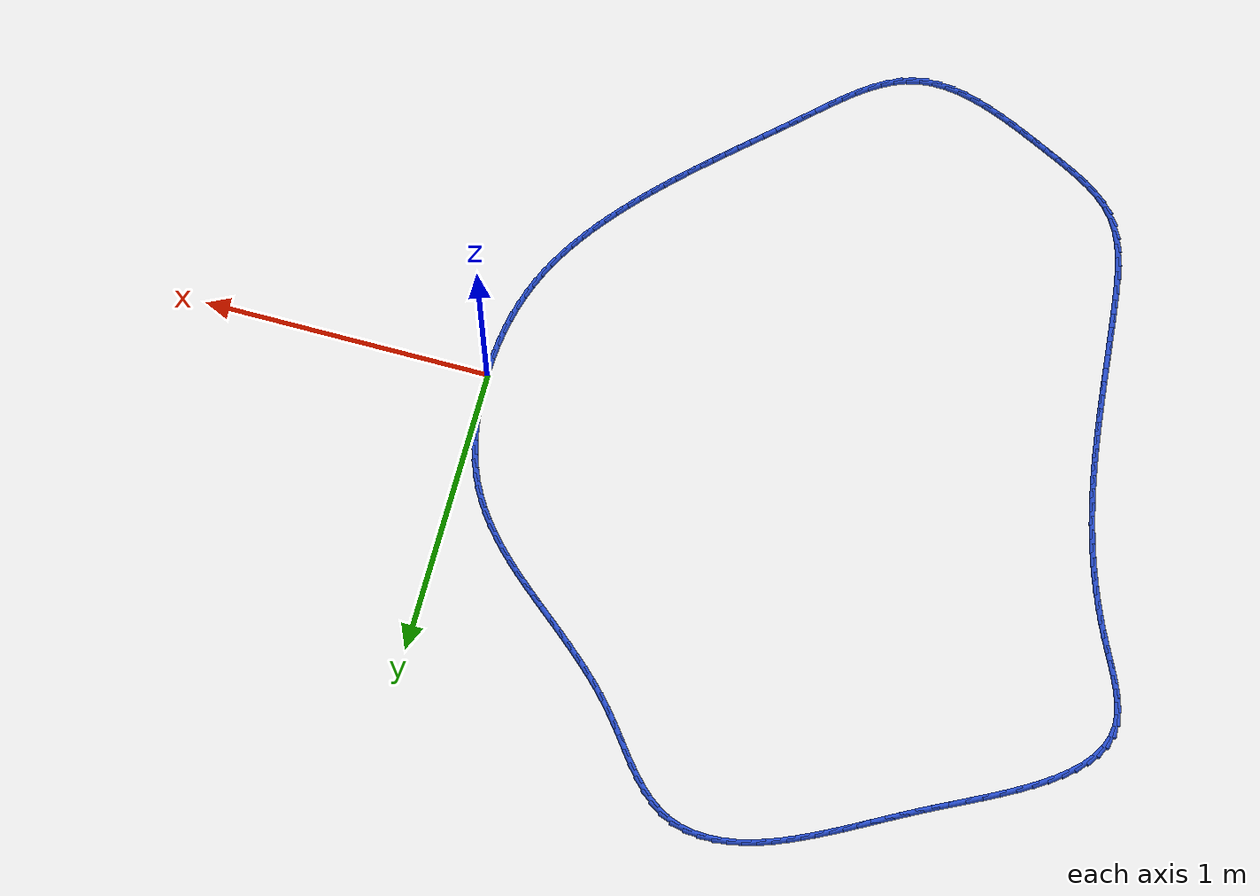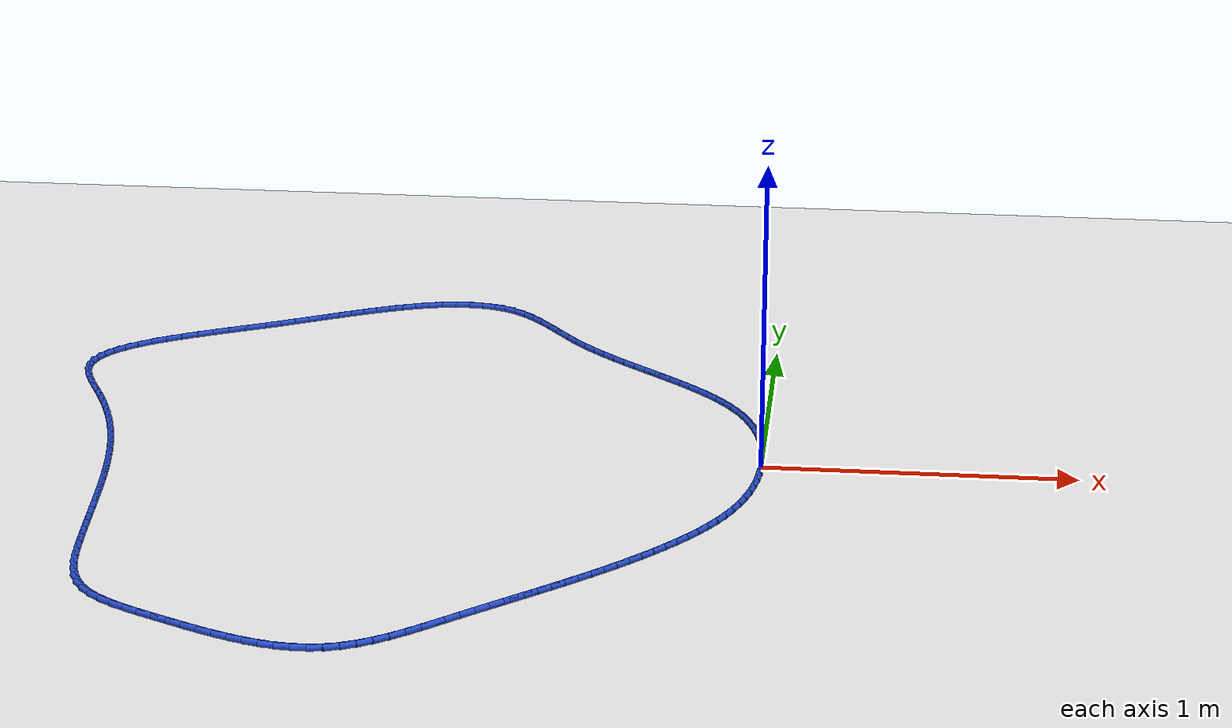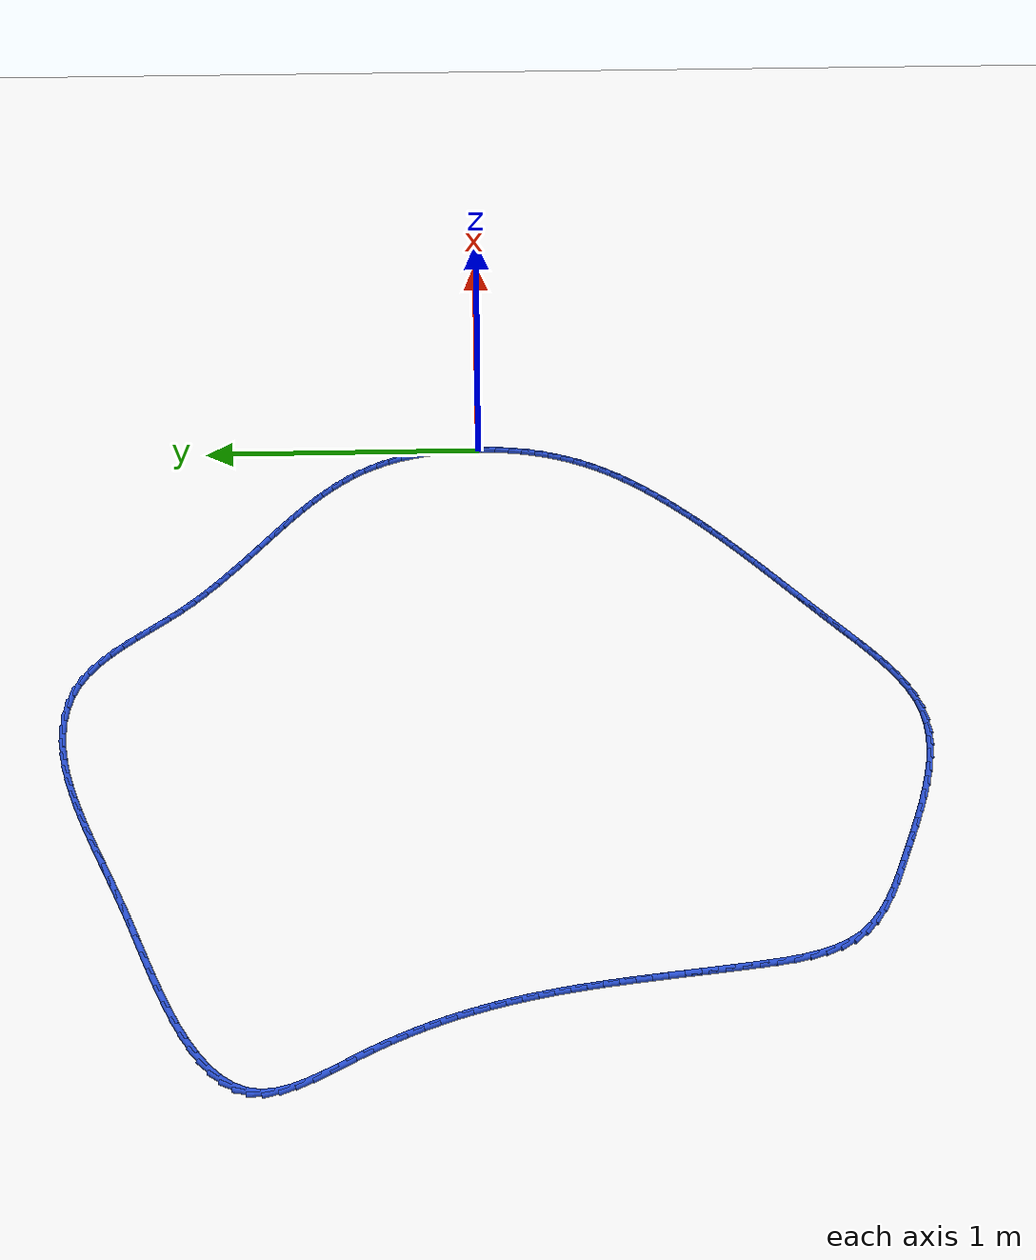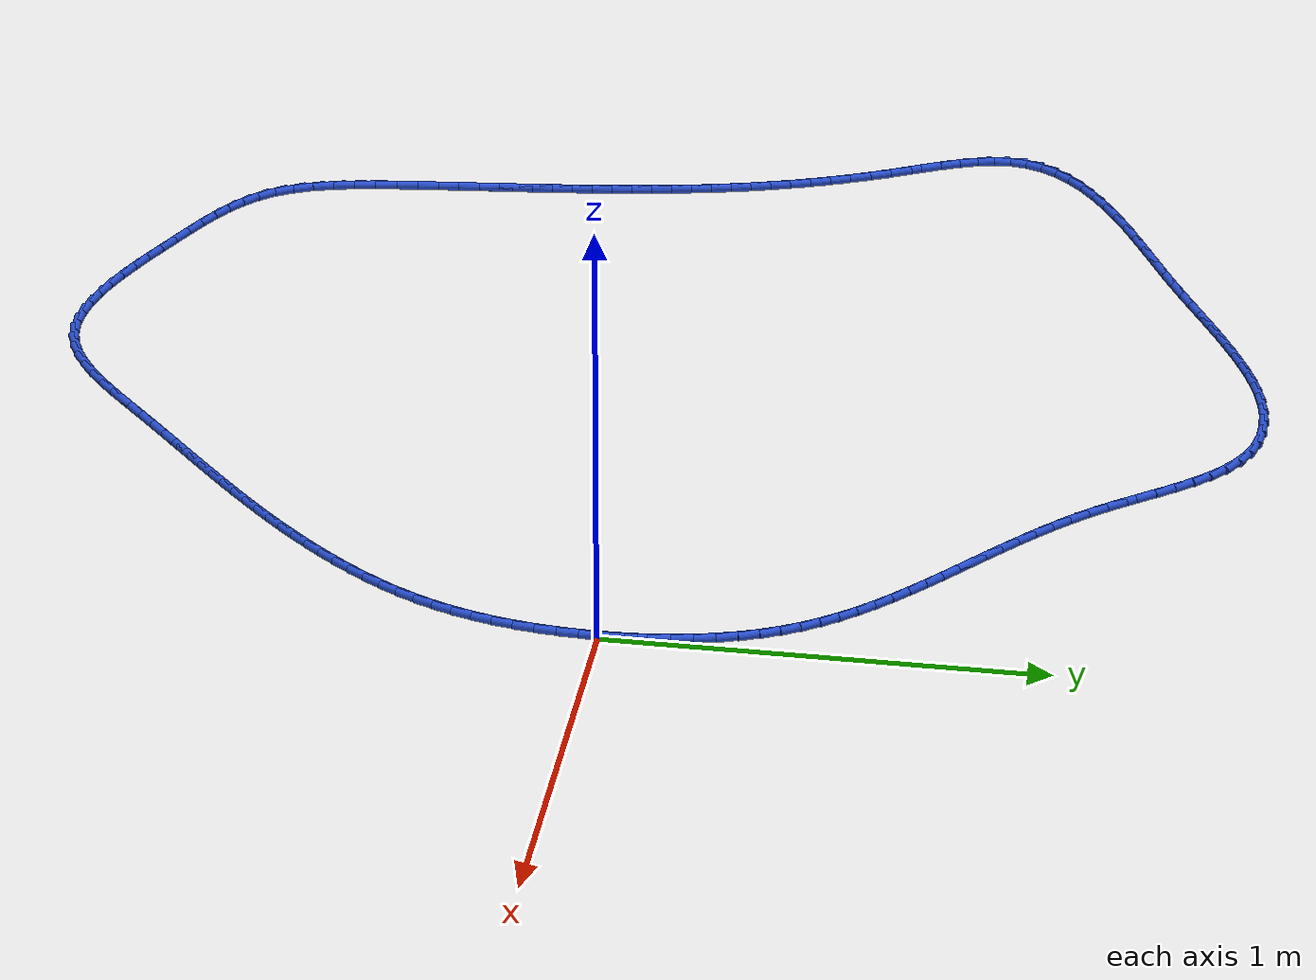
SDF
<sdf version="1.6">
 <world name="default">
  <light name="sun" type="directional">
   <pose>0 0 10 0 -0 0</pose>
   <diffuse>0.8 0.8 0.8 1</diffuse>
   <specular>0.2 0.2 0.2 1</specular>
   <attenuation>
    <range>1000</range>
    <constant>0.9</constant>
    <linear>0.01</linear>
    <quadratic>0.001</quadratic>
   </attenuation>
   <direction>-0.5 0.1 -0.9</direction>
  </light>
  <model name="ground_plane">
   <static>1</static>
   <link name="link">
    <collision name="collision">
     <geometry><plane><normal>0 0 1</normal><size>100 100</size></plane></geometry>
     <surface><friction><ode><mu>100</mu><mu2>50</mu2></ode></friction></surface>
    </collision>
    <visual name="visual">
     <cast_shadows>0</cast_shadows>
     <geometry><plane><normal>0 0 1</normal><size>100 100</size></plane></geometry>
     <material>
      <script><uri>file://media/materials/scripts/gazebo.material</uri><name>Gazebo/WhiteGlow</name></script>
     </material>
    </visual>
   </link>
  </model>
  <gravity>0 0 -9.8</gravity>
  <magnetic_field>6e-06 2.3e-05 -4.2e-05</magnetic_field>
  <atmosphere type="adiabatic"/>
  <physics name="default_physics" default="0" type="ode">
   <max_step_size>0.001</max_step_size>
   <real_time_factor>1</real_time_factor>
   <real_time_update_rate>1000</real_time_update_rate>
  </physics>
  <scene><ambient>0.4 0.4 0.4 1</ambient><background>0.7 0.7 0.7 1</background><shadows>1</shadows></scene>
  <spherical_coordinates>
   <surface_model>EARTH_WGS84</surface_model>
   <latitude_deg>0</latitude_deg>
   <longitude_deg>0</longitude_deg>
   <elevation>0</elevation>
   <heading_deg>0</heading_deg>
  </spherical_coordinates>
  <model name="line">
   <link name="link_0">
    <pose>8.673617379884035e-18 4.163336342344337e-17 0.01 0 1.57 -1.5541414784926617</pose>
    <collision name="collision">
     <geometry><cylinder><radius>0.01</radius><length>0.08</length></cylinder></geometry>
    </collision>
    <visual name="visual">
     <material>
      <script><name>Gazebo/Blue</name><uri>file://media/materials/scripts/gazebo.material</uri></script>
     </material>
     <geometry><cylinder><radius>0.01</radius><length>0.08</length></cylinder></geometry>
    </visual>
   </link>
   <link name="link_1">
    <pose>-0.0008361861503276286 0.05020212846412501 0.01 0 1.57 -1.5087919098441163</pose>
    <collision name="collision">
     <geometry><cylinder><radius>0.01</radius><length>0.08</length></cylinder></geometry>
    </collision>
    <visual name="visual">
     <material>
      <script><name>Gazebo/Blue</name><uri>file://media/materials/scripts/gazebo.material</uri></script>
     </material>
     <geometry><cylinder><radius>0.01</radius><length>0.08</length></cylinder></geometry>
    </visual>
   </link>
   <link name="link_2">
    <pose>-0.003951071527079261 0.10037424088931637 0.01 0 1.57 -1.4608389594381468</pose>
    <collision name="collision">
     <geometry><cylinder><radius>0.01</radius><length>0.08</length></cylinder></geometry>
    </collision>
    <visual name="visual">
     <material>
      <script><name>Gazebo/Blue</name><uri>file://media/materials/scripts/gazebo.material</uri></script>
     </material>
     <geometry><cylinder><radius>0.01</radius><length>0.08</length></cylinder></geometry>
    </visual>
   </link>
   <link name="link_3">
    <pose>-0.009453025080023244 0.15020957049174394 0.01 0 1.57 -1.4096306189398473</pose>
    <collision name="collision">
     <geometry><cylinder><radius>0.01</radius><length>0.08</length></cylinder></geometry>
    </collision>
    <visual name="visual">
     <material>
      <script><name>Gazebo/Blue</name><uri>file://media/materials/scripts/gazebo.material</uri></script>
     </material>
     <geometry><cylinder><radius>0.01</radius><length>0.08</length></cylinder></geometry>
    </visual>
   </link>
   <link name="link_4">
    <pose>-0.017450415758927893 0.19940135048757762 0.01 0 1.57 -1.354481820900038</pose>
    <collision name="collision">
     <geometry><cylinder><radius>0.01</radius><length>0.08</length></cylinder></geometry>
    </collision>
    <visual name="visual">
     <material>
      <script><name>Gazebo/Blue</name><uri>file://media/materials/scripts/gazebo.material</uri></script>
     </material>
     <geometry><cylinder><radius>0.01</radius><length>0.08</length></cylinder></geometry>
    </visual>
   </link>
   <link name="link_5">
    <pose>-0.028051612513561565 0.2476428140929872 0.01 0 1.57 -1.2946770312788471</pose>
    <collision name="collision">
     <geometry><cylinder><radius>0.01</radius><length>0.08</length></cylinder></geometry>
    </collision>
    <visual name="visual">
     <material>
      <script><name>Gazebo/Blue</name><uri>file://media/materials/scripts/gazebo.material</uri></script>
     </material>
     <geometry><cylinder><radius>0.01</radius><length>0.08</length></cylinder></geometry>
    </visual>
   </link>
   <link name="link_6">
    <pose>-0.04136498429369261 0.29462719452414265 0.01 0 1.57 -1.2294859005522079</pose>
    <collision name="collision">
     <geometry><cylinder><radius>0.01</radius><length>0.08</length></cylinder></geometry>
    </collision>
    <visual name="visual">
     <material>
      <script><name>Gazebo/Blue</name><uri>file://media/materials/scripts/gazebo.material</uri></script>
     </material>
     <geometry><cylinder><radius>0.01</radius><length>0.08</length></cylinder></geometry>
    </visual>
   </link>
   <link name="link_7">
    <pose>-0.05749890004908932 0.34004772499721353 0.01 0 1.57 -1.1581981714654466</pose>
    <collision name="collision">
     <geometry><cylinder><radius>0.01</radius><length>0.08</length></cylinder></geometry>
    </collision>
    <visual name="visual">
     <material>
      <script><name>Gazebo/Blue</name><uri>file://media/materials/scripts/gazebo.material</uri></script>
     </material>
     <geometry><cylinder><radius>0.01</radius><length>0.08</length></cylinder></geometry>
    </visual>
   </link>
   <link name="link_8">
    <pose>-0.07656172813389683 0.3835976395973358 0.01 0 1.57 -1.082322276304888</pose>
    <collision name="collision">
     <geometry><cylinder><radius>0.01</radius><length>0.08</length></cylinder></geometry>
    </collision>
    <visual name="visual">
     <material>
      <script><name>Gazebo/Blue</name><uri>file://media/materials/scripts/gazebo.material</uri></script>
     </material>
     <geometry><cylinder><radius>0.01</radius><length>0.08</length></cylinder></geometry>
    </visual>
   </link>
   <link name="link_9">
    <pose>-0.09859789434226914 0.42506345939320184 0.01 0 1.57 -1.0101015547327135</pose>
    <collision name="collision">
     <geometry><cylinder><radius>0.01</radius><length>0.08</length></cylinder></geometry>
    </collision>
    <visual name="visual">
     <material>
      <script><name>Gazebo/Blue</name><uri>file://media/materials/scripts/gazebo.material</uri></script>
     </material>
     <geometry><cylinder><radius>0.01</radius><length>0.08</length></cylinder></geometry>
    </visual>
   </link>
   <link name="link_10">
    <pose>-0.12341201703831871 0.46458156494906105 0.01 0 1.57 -0.9444666118038991</pose>
    <collision name="collision">
     <geometry><cylinder><radius>0.01</radius><length>0.08</length></cylinder></geometry>
    </collision>
    <visual name="visual">
     <material>
      <script><name>Gazebo/Blue</name><uri>file://media/materials/scripts/gazebo.material</uri></script>
     </material>
     <geometry><cylinder><radius>0.01</radius><length>0.08</length></cylinder></geometry>
    </visual>
   </link>
   <link name="link_11">
    <pose>-0.15075250729138104 0.5023703386912153 0.01 0 1.57 -0.8861672792149091</pose>
    <collision name="collision">
     <geometry><cylinder><radius>0.01</radius><length>0.08</length></cylinder></geometry>
    </collision>
    <visual name="visual">
     <material>
      <script><name>Gazebo/Blue</name><uri>file://media/materials/scripts/gazebo.material</uri></script>
     </material>
     <geometry><cylinder><radius>0.01</radius><length>0.08</length></cylinder></geometry>
    </visual>
   </link>
   <link name="link_12">
    <pose>-0.1803677761707916 0.5386481630459661 0.01 0 1.57 -0.835590318260056</pose>
    <collision name="collision">
     <geometry><cylinder><radius>0.01</radius><length>0.08</length></cylinder></geometry>
    </collision>
    <visual name="visual">
     <material>
      <script><name>Gazebo/Blue</name><uri>file://media/materials/scripts/gazebo.material</uri></script>
     </material>
     <geometry><cylinder><radius>0.01</radius><length>0.08</length></cylinder></geometry>
    </visual>
   </link>
   <link name="link_13">
    <pose>-0.21200623474588573 0.5736334204396153 0.01 0 1.57 -0.792840169392454</pose>
    <collision name="collision">
     <geometry><cylinder><radius>0.01</radius><length>0.08</length></cylinder></geometry>
    </collision>
    <visual name="visual">
     <material>
      <script><name>Gazebo/Blue</name><uri>file://media/materials/scripts/gazebo.material</uri></script>
     </material>
     <geometry><cylinder><radius>0.01</radius><length>0.08</length></cylinder></geometry>
    </visual>
   </link>
   <link name="link_14">
    <pose>-0.24541629408599883 0.607544493298464 0.01 0 1.57 -0.7578286116759948</pose>
    <collision name="collision">
     <geometry><cylinder><radius>0.01</radius><length>0.08</length></cylinder></geometry>
    </collision>
    <visual name="visual">
     <material>
      <script><name>Gazebo/Blue</name><uri>file://media/materials/scripts/gazebo.material</uri></script>
     </material>
     <geometry><cylinder><radius>0.01</radius><length>0.08</length></cylinder></geometry>
    </visual>
   </link>
   <link name="link_15">
    <pose>-0.2803463652604664 0.6405997640488145 0.01 0 1.57 -0.7303555322253231</pose>
    <collision name="collision">
     <geometry><cylinder><radius>0.01</radius><length>0.08</length></cylinder></geometry>
    </collision>
    <visual name="visual">
     <material>
      <script><name>Gazebo/Blue</name><uri>file://media/materials/scripts/gazebo.material</uri></script>
     </material>
     <geometry><cylinder><radius>0.01</radius><length>0.08</length></cylinder></geometry>
    </visual>
   </link>
   <link name="link_16">
    <pose>-0.31654485933862386 0.6730176151169678 0.01 0 1.57 -0.7101726313405298</pose>
    <collision name="collision">
     <geometry><cylinder><radius>0.01</radius><length>0.08</length></cylinder></geometry>
    </collision>
    <visual name="visual">
     <material>
      <script><name>Gazebo/Blue</name><uri>file://media/materials/scripts/gazebo.material</uri></script>
     </material>
     <geometry><cylinder><radius>0.01</radius><length>0.08</length></cylinder></geometry>
    </visual>
   </link>
   <link name="link_17">
    <pose>-0.3537601873898068 0.7050164289292263 0.01 0 1.57 -0.6970286506961715</pose>
    <collision name="collision">
     <geometry><cylinder><radius>0.01</radius><length>0.08</length></cylinder></geometry>
    </collision>
    <visual name="visual">
     <material>
      <script><name>Gazebo/Blue</name><uri>file://media/materials/scripts/gazebo.material</uri></script>
     </material>
     <geometry><cylinder><radius>0.01</radius><length>0.08</length></cylinder></geometry>
    </visual>
   </link>
   <link name="link_18">
    <pose>-0.39174076048335027 0.736814587911891 0.01 0 1.57 -0.690698181460474</pose>
    <collision name="collision">
     <geometry><cylinder><radius>0.01</radius><length>0.08</length></cylinder></geometry>
    </collision>
    <visual name="visual">
     <material>
      <script><name>Gazebo/Blue</name><uri>file://media/materials/scripts/gazebo.material</uri></script>
     </material>
     <geometry><cylinder><radius>0.01</radius><length>0.08</length></cylinder></geometry>
    </visual>
   </link>
   <link name="link_19">
    <pose>-0.43023498968859014 0.7686304744912641 0.01 0 1.57 -0.6909971768165832</pose>
    <collision name="collision">
     <geometry><cylinder><radius>0.01</radius><length>0.08</length></cylinder></geometry>
    </collision>
    <visual name="visual">
     <material>
      <script><name>Gazebo/Blue</name><uri>file://media/materials/scripts/gazebo.material</uri></script>
     </material>
     <geometry><cylinder><radius>0.01</radius><length>0.08</length></cylinder></geometry>
    </visual>
   </link>
   <link name="link_20">
    <pose>-0.4689912860748613 0.8006824710936465 0.01 0 1.57 -0.6977880268047785</pose>
    <collision name="collision">
     <geometry><cylinder><radius>0.01</radius><length>0.08</length></cylinder></geometry>
    </collision>
    <visual name="visual">
     <material>
      <script><name>Gazebo/Blue</name><uri>file://media/materials/scripts/gazebo.material</uri></script>
     </material>
     <geometry><cylinder><radius>0.01</radius><length>0.08</length></cylinder></geometry>
    </visual>
   </link>
   <link name="link_21">
    <pose>-0.5077580607114995 0.8331889601453403 0.01 0 1.57 -0.7109762412414513</pose>
    <collision name="collision">
     <geometry><cylinder><radius>0.01</radius><length>0.08</length></cylinder></geometry>
    </collision>
    <visual name="visual">
     <material>
      <script><name>Gazebo/Blue</name><uri>file://media/materials/scripts/gazebo.material</uri></script>
     </material>
     <geometry><cylinder><radius>0.01</radius><length>0.08</length></cylinder></geometry>
    </visual>
   </link>
   <link name="link_22">
    <pose>-0.5462837246678405 0.8663683240726474 0.01 0 1.57 -0.7304998987826888</pose>
    <collision name="collision">
     <geometry><cylinder><radius>0.01</radius><length>0.08</length></cylinder></geometry>
    </collision>
    <visual name="visual">
     <material>
      <script><name>Gazebo/Blue</name><uri>file://media/materials/scripts/gazebo.material</uri></script>
     </material>
     <geometry><cylinder><radius>0.01</radius><length>0.08</length></cylinder></geometry>
    </visual>
   </link>
   <link name="link_23">
    <pose>-0.5843166890132192 0.9004389453018689 0.01 0 1.57 -0.7563123185710312</pose>
    <collision name="collision">
     <geometry><cylinder><radius>0.01</radius><length>0.08</length></cylinder></geometry>
    </collision>
    <visual name="visual">
     <material>
      <script><name>Gazebo/Blue</name><uri>file://media/materials/scripts/gazebo.material</uri></script>
     </material>
     <geometry><cylinder><radius>0.01</radius><length>0.08</length></cylinder></geometry>
    </visual>
   </link>
   <link name="link_24">
    <pose>-0.621605364816971 0.9356192062593068 0.01 0 1.57 -0.7883580665600509</pose>
    <collision name="collision">
     <geometry><cylinder><radius>0.01</radius><length>0.08</length></cylinder></geometry>
    </collision>
    <visual name="visual">
     <material>
      <script><name>Gazebo/Blue</name><uri>file://media/materials/scripts/gazebo.material</uri></script>
     </material>
     <geometry><cylinder><radius>0.01</radius><length>0.08</length></cylinder></geometry>
    </visual>
   </link>
   <link name="link_25">
    <pose>-0.6578981631484317 0.9721274893712625 0.01 0 1.57 -0.8265425768473195</pose>
    <collision name="collision">
     <geometry><cylinder><radius>0.01</radius><length>0.08</length></cylinder></geometry>
    </collision>
    <visual name="visual">
     <material>
      <script><name>Gazebo/Blue</name><uri>file://media/materials/scripts/gazebo.material</uri></script>
     </material>
     <geometry><cylinder><radius>0.01</radius><length>0.08</length></cylinder></geometry>
    </visual>
   </link>
   <link name="link_26">
    <pose>-0.6929434950769366 1.0101821770640378 0.01 0 1.57 -0.8700380516673217</pose>
    <collision name="collision">
     <geometry><cylinder><radius>0.01</radius><length>0.08</length></cylinder></geometry>
    </collision>
    <visual name="visual">
     <material>
      <script><name>Gazebo/Blue</name><uri>file://media/materials/scripts/gazebo.material</uri></script>
     </material>
     <geometry><cylinder><radius>0.01</radius><length>0.08</length></cylinder></geometry>
    </visual>
   </link>
   <link name="link_27">
    <pose>-0.7265103654717305 1.0499728950049874 0.01 0 1.57 -0.9050285195846655</pose>
    <collision name="collision">
     <geometry><cylinder><radius>0.01</radius><length>0.08</length></cylinder></geometry>
    </collision>
    <visual name="visual">
     <material>
      <script><name>Gazebo/Blue</name><uri>file://media/materials/scripts/gazebo.material</uri></script>
     </material>
     <geometry><cylinder><radius>0.01</radius><length>0.08</length></cylinder></geometry>
    </visual>
   </link>
   <link name="link_28">
    <pose>-0.7587999576994333 1.0910857836899053 0.01 0 1.57 -0.9190451656950118</pose>
    <collision name="collision">
     <geometry><cylinder><radius>0.01</radius><length>0.08</length></cylinder></geometry>
    </collision>
    <visual name="visual">
     <material>
      <script><name>Gazebo/Blue</name><uri>file://media/materials/scripts/gazebo.material</uri></script>
     </material>
     <geometry><cylinder><radius>0.01</radius><length>0.08</length></cylinder></geometry>
    </visual>
   </link>
   <link name="link_29">
    <pose>-0.7904237734903216 1.132534023484484 0.01 0 1.57 -0.9117036804917791</pose>
    <collision name="collision">
     <geometry><cylinder><radius>0.01</radius><length>0.08</length></cylinder></geometry>
    </collision>
    <visual name="visual">
     <material>
      <script><name>Gazebo/Blue</name><uri>file://media/materials/scripts/gazebo.material</uri></script>
     </material>
     <geometry><cylinder><radius>0.01</radius><length>0.08</length></cylinder></geometry>
    </visual>
   </link>
   <link name="link_30">
    <pose>-0.8220095326550254 1.1733081481603207 0.01 0 1.57 -0.882127927729454</pose>
    <collision name="collision">
     <geometry><cylinder><radius>0.01</radius><length>0.08</length></cylinder></geometry>
    </collision>
    <visual name="visual">
     <material>
      <script><name>Gazebo/Blue</name><uri>file://media/materials/scripts/gazebo.material</uri></script>
     </material>
     <geometry><cylinder><radius>0.01</radius><length>0.08</length></cylinder></geometry>
    </visual>
   </link>
   <link name="link_31">
    <pose>-0.8541849550041767 1.2123986914890155 0.01 0 1.57 -0.8284247151423396</pose>
    <collision name="collision">
     <geometry><cylinder><radius>0.01</radius><length>0.08</length></cylinder></geometry>
    </collision>
    <visual name="visual">
     <material>
      <script><name>Gazebo/Blue</name><uri>file://media/materials/scripts/gazebo.material</uri></script>
     </material>
     <geometry><cylinder><radius>0.01</radius><length>0.08</length></cylinder></geometry>
    </visual>
   </link>
   <link name="link_32">
    <pose>-0.8875777603484063 1.2487961872421658 0.01 0 1.57 -0.7479827161989426</pose>
    <collision name="collision">
     <geometry><cylinder><radius>0.01</radius><length>0.08</length></cylinder></geometry>
    </collision>
    <visual name="visual">
     <material>
      <script><name>Gazebo/Blue</name><uri>file://media/materials/scripts/gazebo.material</uri></script>
     </material>
     <geometry><cylinder><radius>0.01</radius><length>0.08</length></cylinder></geometry>
    </visual>
   </link>
   <link name="link_33">
    <pose>-0.9228156684983457 1.2814911691913706 0.01 0 1.57 -0.6383894587282689</pose>
    <collision name="collision">
     <geometry><cylinder><radius>0.01</radius><length>0.08</length></cylinder></geometry>
    </collision>
    <visual name="visual">
     <material>
      <script><name>Gazebo/Blue</name><uri>file://media/materials/scripts/gazebo.material</uri></script>
     </material>
     <geometry><cylinder><radius>0.01</radius><length>0.08</length></cylinder></geometry>
    </visual>
   </link>
   <link name="link_34">
    <pose>-0.9605263992646258 1.3094741711082285 0.01 0 1.57 -0.4993629846260897</pose>
    <collision name="collision">
     <geometry><cylinder><radius>0.01</radius><length>0.08</length></cylinder></geometry>
    </collision>
    <visual name="visual">
     <material>
      <script><name>Gazebo/Blue</name><uri>file://media/materials/scripts/gazebo.material</uri></script>
     </material>
     <geometry><cylinder><radius>0.01</radius><length>0.08</length></cylinder></geometry>
    </visual>
   </link>
   <link name="link_35">
    <pose>-1.0013376724578775 1.3317357267643382 0.01 0 1.57 -0.335885140248361</pose>
    <collision name="collision">
     <geometry><cylinder><radius>0.01</radius><length>0.08</length></cylinder></geometry>
    </collision>
    <visual name="visual">
     <material>
      <script><name>Gazebo/Blue</name><uri>file://media/materials/scripts/gazebo.material</uri></script>
     </material>
     <geometry><cylinder><radius>0.01</radius><length>0.08</length></cylinder></geometry>
    </visual>
   </link>
   <link name="link_36">
    <pose>-1.0458603045078667 1.347279193356961 0.01 0 1.57 -0.17585779612044228</pose>
    <collision name="collision">
     <geometry><cylinder><radius>0.01</radius><length>0.08</length></cylinder></geometry>
    </collision>
    <visual name="visual">
     <material>
      <script><name>Gazebo/Blue</name><uri>file://media/materials/scripts/gazebo.material</uri></script>
     </material>
     <geometry><cylinder><radius>0.01</radius><length>0.08</length></cylinder></geometry>
    </visual>
   </link>
   <link name="link_37">
    <pose>-1.093796598112448 1.3557971545994862 0.01 0 1.57 -0.04442846576390625</pose>
    <collision name="collision">
     <geometry><cylinder><radius>0.01</radius><length>0.08</length></cylinder></geometry>
    </collision>
    <visual name="visual">
     <material>
      <script><name>Gazebo/Blue</name><uri>file://media/materials/scripts/gazebo.material</uri></script>
     </material>
     <geometry><cylinder><radius>0.01</radius><length>0.08</length></cylinder></geometry>
    </visual>
   </link>
   <link name="link_38">
    <pose>-1.1434982857844074 1.3580067783703487 0.01 0 1.57 0.06623231749179008</pose>
    <collision name="collision">
     <geometry><cylinder><radius>0.01</radius><length>0.08</length></cylinder></geometry>
    </collision>
    <visual name="visual">
     <material>
      <script><name>Gazebo/Blue</name><uri>file://media/materials/scripts/gazebo.material</uri></script>
     </material>
     <geometry><cylinder><radius>0.01</radius><length>0.08</length></cylinder></geometry>
    </visual>
   </link>
   <link name="link_39">
    <pose>-1.1932443402994146 1.3547071556419354 0.01 0 1.57 0.16297169116956914</pose>
    <collision name="collision">
     <geometry><cylinder><radius>0.01</radius><length>0.08</length></cylinder></geometry>
    </collision>
    <visual name="visual">
     <material>
      <script><name>Gazebo/Blue</name><uri>file://media/materials/scripts/gazebo.material</uri></script>
     </material>
     <geometry><cylinder><radius>0.01</radius><length>0.08</length></cylinder></geometry>
    </visual>
   </link>
   <link name="link_40">
    <pose>-1.2421309132966816 1.3466687356337397 0.01 0 1.57 0.2460404690639701</pose>
    <collision name="collision">
     <geometry><cylinder><radius>0.01</radius><length>0.08</length></cylinder></geometry>
    </collision>
    <visual name="visual">
     <material>
      <script><name>Gazebo/Blue</name><uri>file://media/materials/scripts/gazebo.material</uri></script>
     </material>
     <geometry><cylinder><radius>0.01</radius><length>0.08</length></cylinder></geometry>
    </visual>
   </link>
   <link name="link_41">
    <pose>-1.2900537725105432 1.3346339413795165 0.01 0 1.57 0.3152193739012006</pose>
    <collision name="collision">
     <geometry><cylinder><radius>0.01</radius><length>0.08</length></cylinder></geometry>
    </collision>
    <visual name="visual">
     <material>
      <script><name>Gazebo/Blue</name><uri>file://media/materials/scripts/gazebo.material</uri></script>
     </material>
     <geometry><cylinder><radius>0.01</radius><length>0.08</length></cylinder></geometry>
    </visual>
   </link>
   <link name="link_42">
    <pose>-1.3369421073820538 1.3193440244971821 0.01 0 1.57 0.3708777782731771</pose>
    <collision name="collision">
     <geometry><cylinder><radius>0.01</radius><length>0.08</length></cylinder></geometry>
    </collision>
    <visual name="visual">
     <material>
      <script><name>Gazebo/Blue</name><uri>file://media/materials/scripts/gazebo.material</uri></script>
     </material>
     <geometry><cylinder><radius>0.01</radius><length>0.08</length></cylinder></geometry>
    </visual>
   </link>
   <link name="link_43">
    <pose>-1.3827251073522688 1.3015402366046527 0.01 0 1.57 0.4135559494841368</pose>
    <collision name="collision">
     <geometry><cylinder><radius>0.01</radius><length>0.08</length></cylinder></geometry>
    </collision>
    <visual name="visual">
     <material>
      <script><name>Gazebo/Blue</name><uri>file://media/materials/scripts/gazebo.material</uri></script>
     </material>
     <geometry><cylinder><radius>0.01</radius><length>0.08</length></cylinder></geometry>
    </visual>
   </link>
   <link name="link_44">
    <pose>-1.427331961862243 1.2819638293198428 0.01 0 1.57 0.4439012300855681</pose>
    <collision name="collision">
     <geometry><cylinder><radius>0.01</radius><length>0.08</length></cylinder></geometry>
    </collision>
    <visual name="visual">
     <material>
      <script><name>Gazebo/Blue</name><uri>file://media/materials/scripts/gazebo.material</uri></script>
     </material>
     <geometry><cylinder><radius>0.01</radius><length>0.08</length></cylinder></geometry>
    </visual>
   </link>
   <link name="link_45">
    <pose>-1.4707045840906736 1.261337753399725 0.01 0 1.57 0.46633279466937677</pose>
    <collision name="collision">
     <geometry><cylinder><radius>0.01</radius><length>0.08</length></cylinder></geometry>
    </collision>
    <visual name="visual">
     <material>
      <script><name>Gazebo/Blue</name><uri>file://media/materials/scripts/gazebo.material</uri></script>
     </material>
     <geometry><cylinder><radius>0.01</radius><length>0.08</length></cylinder></geometry>
    </visual>
   </link>
   <link name="link_46">
    <pose>-1.513029591768719 1.2400329950989366 0.01 0 1.57 0.4843009011762244</pose>
    <collision name="collision">
     <geometry><cylinder><radius>0.01</radius><length>0.08</length></cylinder></geometry>
    </collision>
    <visual name="visual">
     <material>
      <script><name>Gazebo/Blue</name><uri>file://media/materials/scripts/gazebo.material</uri></script>
     </material>
     <geometry><cylinder><radius>0.01</radius><length>0.08</length></cylinder></geometry>
    </visual>
   </link>
   <link name="link_47">
    <pose>-1.5547143095187024 1.2181030925889966 0.01 0 1.57 0.4974584027793289</pose>
    <collision name="collision">
     <geometry><cylinder><radius>0.01</radius><length>0.08</length></cylinder></geometry>
    </collision>
    <visual name="visual">
     <material>
      <script><name>Gazebo/Blue</name><uri>file://media/materials/scripts/gazebo.material</uri></script>
     </material>
     <geometry><cylinder><radius>0.01</radius><length>0.08</length></cylinder></geometry>
    </visual>
   </link>
   <link name="link_48">
    <pose>-1.5961739701337823 1.1955902095271986 0.01 0 1.57 0.5055358548718742</pose>
    <collision name="collision">
     <geometry><cylinder><radius>0.01</radius><length>0.08</length></cylinder></geometry>
    </collision>
    <visual name="visual">
     <material>
      <script><name>Gazebo/Blue</name><uri>file://media/materials/scripts/gazebo.material</uri></script>
     </material>
     <geometry><cylinder><radius>0.01</radius><length>0.08</length></cylinder></geometry>
    </visual>
   </link>
   <link name="link_49">
    <pose>-1.637823806407116 1.172536509570838 0.01 0 1.57 0.5084938304719454</pose>
    <collision name="collision">
     <geometry><cylinder><radius>0.01</radius><length>0.08</length></cylinder></geometry>
    </collision>
    <visual name="visual">
     <material>
      <script><name>Gazebo/Blue</name><uri>file://media/materials/scripts/gazebo.material</uri></script>
     </material>
     <geometry><cylinder><radius>0.01</radius><length>0.08</length></cylinder></geometry>
    </visual>
   </link>
   <link name="link_50">
    <pose>-1.6800790511318628 1.1489841563772087 0.01 0 1.57 0.5065100277480074</pose>
    <collision name="collision">
     <geometry><cylinder><radius>0.01</radius><length>0.08</length></cylinder></geometry>
    </collision>
    <visual name="visual">
     <material>
      <script><name>Gazebo/Blue</name><uri>file://media/materials/scripts/gazebo.material</uri></script>
     </material>
     <geometry><cylinder><radius>0.01</radius><length>0.08</length></cylinder></geometry>
    </visual>
   </link>
   <link name="link_51">
    <pose>-1.7233549371011816 1.1249753136036051 0.01 0 1.57 0.499948718249997</pose>
    <collision name="collision">
     <geometry><cylinder><radius>0.01</radius><length>0.08</length></cylinder></geometry>
    </collision>
    <visual name="visual">
     <material>
      <script><name>Gazebo/Blue</name><uri>file://media/materials/scripts/gazebo.material</uri></script>
     </material>
     <geometry><cylinder><radius>0.01</radius><length>0.08</length></cylinder></geometry>
    </visual>
   </link>
   <link name="link_52">
    <pose>-1.7680666971082293 1.1005521449073217 0.01 0 1.57 0.4893184250599927</pose>
    <collision name="collision">
     <geometry><cylinder><radius>0.01</radius><length>0.08</length></cylinder></geometry>
    </collision>
    <visual name="visual">
     <material>
      <script><name>Gazebo/Blue</name><uri>file://media/materials/scripts/gazebo.material</uri></script>
     </material>
     <geometry><cylinder><radius>0.01</radius><length>0.08</length></cylinder></geometry>
    </visual>
   </link>
   <link name="link_53">
    <pose>-1.8146295639461658 1.075756813945653 0.01 0 1.57 0.47633355521950715</pose>
    <collision name="collision">
     <geometry><cylinder><radius>0.01</radius><length>0.08</length></cylinder></geometry>
    </collision>
    <visual name="visual">
     <material>
      <script><name>Gazebo/Blue</name><uri>file://media/materials/scripts/gazebo.material</uri></script>
     </material>
     <geometry><cylinder><radius>0.01</radius><length>0.08</length></cylinder></geometry>
    </visual>
   </link>
   <link name="link_54">
    <pose>-1.8633533335800454 1.0506173211661138 0.01 0 1.57 0.469280866320584</pose>
    <collision name="collision">
     <geometry><cylinder><radius>0.01</radius><length>0.08</length></cylinder></geometry>
    </collision>
    <visual name="visual">
     <material>
      <script><name>Gazebo/Blue</name><uri>file://media/materials/scripts/gazebo.material</uri></script>
     </material>
     <geometry><cylinder><radius>0.01</radius><length>0.08</length></cylinder></geometry>
    </visual>
   </link>
   <link name="link_55">
    <pose>-1.913763425362137 1.0250563025936206 0.01 0 1.57 0.47100540974582433</pose>
    <collision name="collision">
     <geometry><cylinder><radius>0.01</radius><length>0.08</length></cylinder></geometry>
    </collision>
    <visual name="visual">
     <material>
      <script><name>Gazebo/Blue</name><uri>file://media/materials/scripts/gazebo.material</uri></script>
     </material>
     <geometry><cylinder><radius>0.01</radius><length>0.08</length></cylinder></geometry>
    </visual>
   </link>
   <link name="link_56">
    <pose>-1.9650316802480123 0.9989488984672614 0.01 0 1.57 0.4811241999632559</pose>
    <collision name="collision">
     <geometry><cylinder><radius>0.01</radius><length>0.08</length></cylinder></geometry>
    </collision>
    <visual name="visual">
     <material>
      <script><name>Gazebo/Blue</name><uri>file://media/materials/scripts/gazebo.material</uri></script>
     </material>
     <geometry><cylinder><radius>0.01</radius><length>0.08</length></cylinder></geometry>
    </visual>
   </link>
   <link name="link_57">
    <pose>-2.0163282276544376 0.9721700191170536 0.01 0 1.57 0.4998461972336203</pose>
    <collision name="collision">
     <geometry><cylinder><radius>0.01</radius><length>0.08</length></cylinder></geometry>
    </collision>
    <visual name="visual">
     <material>
      <script><name>Gazebo/Blue</name><uri>file://media/materials/scripts/gazebo.material</uri></script>
     </material>
     <geometry><cylinder><radius>0.01</radius><length>0.08</length></cylinder></geometry>
    </visual>
   </link>
   <link name="link_58">
    <pose>-2.0668231969981807 0.9445945748730139 0.01 0 1.57 0.5279733349756276</pose>
    <collision name="collision">
     <geometry><cylinder><radius>0.01</radius><length>0.08</length></cylinder></geometry>
    </collision>
    <visual name="visual">
     <material>
      <script><name>Gazebo/Blue</name><uri>file://media/materials/scripts/gazebo.material</uri></script>
     </material>
     <geometry><cylinder><radius>0.01</radius><length>0.08</length></cylinder></geometry>
    </visual>
   </link>
   <link name="link_59">
    <pose>-2.1156867176960095 0.9160974760651602 0.01 0 1.57 0.5669618666240649</pose>
    <collision name="collision">
     <geometry><cylinder><radius>0.01</radius><length>0.08</length></cylinder></geometry>
    </collision>
    <visual name="visual">
     <material>
      <script><name>Gazebo/Blue</name><uri>file://media/materials/scripts/gazebo.material</uri></script>
     </material>
     <geometry><cylinder><radius>0.01</radius><length>0.08</length></cylinder></geometry>
    </visual>
   </link>
   <link name="link_60">
    <pose>-2.1620889191646917 0.88655363302351 0.01 0 1.57 0.6190519173948954</pose>
    <collision name="collision">
     <geometry><cylinder><radius>0.01</radius><length>0.08</length></cylinder></geometry>
    </collision>
    <visual name="visual">
     <material>
      <script><name>Gazebo/Blue</name><uri>file://media/materials/scripts/gazebo.material</uri></script>
     </material>
     <geometry><cylinder><radius>0.01</radius><length>0.08</length></cylinder></geometry>
    </visual>
   </link>
   <link name="link_61">
    <pose>-2.2051999308209944 0.8558379560780796 0.01 0 1.57 0.6874436507166901</pose>
    <collision name="collision">
     <geometry><cylinder><radius>0.01</radius><length>0.08</length></cylinder></geometry>
    </collision>
    <visual name="visual">
     <material>
      <script><name>Gazebo/Blue</name><uri>file://media/materials/scripts/gazebo.material</uri></script>
     </material>
     <geometry><cylinder><radius>0.01</radius><length>0.08</length></cylinder></geometry>
    </visual>
   </link>
   <link name="link_62">
    <pose>-2.2441898820816855 0.8238253555588873 0.01 0 1.57 0.776440733396622</pose>
    <collision name="collision">
     <geometry><cylinder><radius>0.01</radius><length>0.08</length></cylinder></geometry>
    </collision>
    <visual name="visual">
     <material>
      <script><name>Gazebo/Blue</name><uri>file://media/materials/scripts/gazebo.material</uri></script>
     </material>
     <geometry><cylinder><radius>0.01</radius><length>0.08</length></cylinder></geometry>
    </visual>
   </link>
   <link name="link_63">
    <pose>-2.278228902363531 0.7903907417959494 0.01 0 1.57 0.8913175580256163</pose>
    <collision name="collision">
     <geometry><cylinder><radius>0.01</radius><length>0.08</length></cylinder></geometry>
    </collision>
    <visual name="visual">
     <material>
      <script><name>Gazebo/Blue</name><uri>file://media/materials/scripts/gazebo.material</uri></script>
     </material>
     <geometry><cylinder><radius>0.01</radius><length>0.08</length></cylinder></geometry>
    </visual>
   </link>
   <link name="link_64">
    <pose>-2.3064871210833005 0.7554090251192842 0.01 0 1.57 1.0373223645908425</pose>
    <collision name="collision">
     <geometry><cylinder><radius>0.01</radius><length>0.08</length></cylinder></geometry>
    </collision>
    <visual name="visual">
     <material>
      <script><name>Gazebo/Blue</name><uri>file://media/materials/scripts/gazebo.material</uri></script>
     </material>
     <geometry><cylinder><radius>0.01</radius><length>0.08</length></cylinder></geometry>
    </visual>
   </link>
   <link name="link_65">
    <pose>-2.32813466765776 0.7187551158589084 0.01 0 1.57 1.2168725509842635</pose>
    <collision name="collision">
     <geometry><cylinder><radius>0.01</radius><length>0.08</length></cylinder></geometry>
    </collision>
    <visual name="visual">
     <material>
      <script><name>Gazebo/Blue</name><uri>file://media/materials/scripts/gazebo.material</uri></script>
     </material>
     <geometry><cylinder><radius>0.01</radius><length>0.08</length></cylinder></geometry>
    </visual>
   </link>
   <link name="link_66">
    <pose>-2.3423416715036787 0.6803039243448393 0.01 0 1.57 1.4248009967054336</pose>
    <collision name="collision">
     <geometry><cylinder><radius>0.01</radius><length>0.08</length></cylinder></geometry>
    </collision>
    <visual name="visual">
     <material>
      <script><name>Gazebo/Blue</name><uri>file://media/materials/scripts/gazebo.material</uri></script>
     </material>
     <geometry><cylinder><radius>0.01</radius><length>0.08</length></cylinder></geometry>
    </visual>
   </link>
   <link name="link_67">
    <pose>-2.348278262037822 0.6399303609070944 0.01 0 1.57 -1.5022703961881914</pose>
    <collision name="collision">
     <geometry><cylinder><radius>0.01</radius><length>0.08</length></cylinder></geometry>
    </collision>
    <visual name="visual">
     <material>
      <script><name>Gazebo/Blue</name><uri>file://media/materials/scripts/gazebo.material</uri></script>
     </material>
     <geometry><cylinder><radius>0.01</radius><length>0.08</length></cylinder></geometry>
    </visual>
   </link>
   <link name="link_68">
    <pose>-2.34537005692187 0.5975573271525267 0.01 0 1.57 -1.3340217669555645</pose>
    <collision name="collision">
     <geometry><cylinder><radius>0.01</radius><length>0.08</length></cylinder></geometry>
    </collision>
    <visual name="visual">
     <material>
      <script><name>Gazebo/Blue</name><uri>file://media/materials/scripts/gazebo.material</uri></script>
     </material>
     <geometry><cylinder><radius>0.01</radius><length>0.08</length></cylinder></geometry>
    </visual>
   </link>
   <link name="link_69">
    <pose>-2.3347203768949876 0.5534228668303172 0.01 0 1.57 -1.2209704856573433</pose>
    <collision name="collision">
     <geometry><cylinder><radius>0.01</radius><length>0.08</length></cylinder></geometry>
    </collision>
    <visual name="visual">
     <material>
      <script><name>Gazebo/Blue</name><uri>file://media/materials/scripts/gazebo.material</uri></script>
     </material>
     <geometry><cylinder><radius>0.01</radius><length>0.08</length></cylinder></geometry>
    </visual>
   </link>
   <link name="link_70">
    <pose>-2.3181093561104293 0.5078921572880356 0.01 0 1.57 -1.1508447634654346</pose>
    <collision name="collision">
     <geometry><cylinder><radius>0.01</radius><length>0.08</length></cylinder></geometry>
    </collision>
    <visual name="visual">
     <material>
      <script><name>Gazebo/Blue</name><uri>file://media/materials/scripts/gazebo.material</uri></script>
     </material>
     <geometry><cylinder><radius>0.01</radius><length>0.08</length></cylinder></geometry>
    </visual>
   </link>
   <link name="link_71">
    <pose>-2.297319005220274 0.4613307283574714 0.01 0 1.57 -1.114384831158453</pose>
    <collision name="collision">
     <geometry><cylinder><radius>0.01</radius><length>0.08</length></cylinder></geometry>
    </collision>
    <visual name="visual">
     <material>
      <script><name>Gazebo/Blue</name><uri>file://media/materials/scripts/gazebo.material</uri></script>
     </material>
     <geometry><cylinder><radius>0.01</radius><length>0.08</length></cylinder></geometry>
    </visual>
   </link>
   <link name="link_72">
    <pose>-2.2741313348765977 0.4141041098704147 0.01 0 1.57 -1.106478323553205</pose>
    <collision name="collision">
     <geometry><cylinder><radius>0.01</radius><length>0.08</length></cylinder></geometry>
    </collision>
    <visual name="visual">
     <material>
      <script><name>Gazebo/Blue</name><uri>file://media/materials/scripts/gazebo.material</uri></script>
     </material>
     <geometry><cylinder><radius>0.01</radius><length>0.08</length></cylinder></geometry>
    </visual>
   </link>
   <link name="link_73">
    <pose>-2.2503283557314777 0.36657783165865415 0.01 0 1.57 -1.1245751413986822</pose>
    <collision name="collision">
     <geometry><cylinder><radius>0.01</radius><length>0.08</length></cylinder></geometry>
    </collision>
    <visual name="visual">
     <material>
      <script><name>Gazebo/Blue</name><uri>file://media/materials/scripts/gazebo.material</uri></script>
     </material>
     <geometry><cylinder><radius>0.01</radius><length>0.08</length></cylinder></geometry>
    </visual>
   </link>
   <link name="link_74">
    <pose>-2.2276154434871844 0.3191013025340409 0.01 0 1.57 -1.1537302645591039</pose>
    <collision name="collision">
     <geometry><cylinder><radius>0.01</radius><length>0.08</length></cylinder></geometry>
    </collision>
    <visual name="visual">
     <material>
      <script><name>Gazebo/Blue</name><uri>file://media/materials/scripts/gazebo.material</uri></script>
     </material>
     <geometry><cylinder><radius>0.01</radius><length>0.08</length></cylinder></geometry>
    </visual>
   </link>
   <link name="link_75">
    <pose>-2.2066607625946713 0.2718057423058133 0.01 0 1.57 -1.1826676853516933</pose>
    <collision name="collision">
     <geometry><cylinder><radius>0.01</radius><length>0.08</length></cylinder></geometry>
    </collision>
    <visual name="visual">
     <material>
      <script><name>Gazebo/Blue</name><uri>file://media/materials/scripts/gazebo.material</uri></script>
     </material>
     <geometry><cylinder><radius>0.01</radius><length>0.08</length></cylinder></geometry>
    </visual>
   </link>
   <link name="link_76">
    <pose>-2.187386560130873 0.22466545870993546 0.01 0 1.57 -1.2109527884124944</pose>
    <collision name="collision">
     <geometry><cylinder><radius>0.01</radius><length>0.08</length></cylinder></geometry>
    </collision>
    <visual name="visual">
     <material>
      <script><name>Gazebo/Blue</name><uri>file://media/materials/scripts/gazebo.material</uri></script>
     </material>
     <geometry><cylinder><radius>0.01</radius><length>0.08</length></cylinder></geometry>
    </visual>
   </link>
   <link name="link_77">
    <pose>-2.169698699184085 0.17765131292687503 0.01 0 1.57 -1.2384067783180133</pose>
    <collision name="collision">
     <geometry><cylinder><radius>0.01</radius><length>0.08</length></cylinder></geometry>
    </collision>
    <visual name="visual">
     <material>
      <script><name>Gazebo/Blue</name><uri>file://media/materials/scripts/gazebo.material</uri></script>
     </material>
     <geometry><cylinder><radius>0.01</radius><length>0.08</length></cylinder></geometry>
    </visual>
   </link>
   <link name="link_78">
    <pose>-2.153503042842599 0.13073416613709743 0.01 0 1.57 -1.2648577319237861</pose>
    <collision name="collision">
     <geometry><cylinder><radius>0.01</radius><length>0.08</length></cylinder></geometry>
    </collision>
    <visual name="visual">
     <material>
      <script><name>Gazebo/Blue</name><uri>file://media/materials/scripts/gazebo.material</uri></script>
     </material>
     <geometry><cylinder><radius>0.01</radius><length>0.08</length></cylinder></geometry>
    </visual>
   </link>
   <link name="link_79">
    <pose>-2.138705454194708 0.08388487952107039 0.01 0 1.57 -1.290143794603306</pose>
    <collision name="collision">
     <geometry><cylinder><radius>0.01</radius><length>0.08</length></cylinder></geometry>
    </collision>
    <visual name="visual">
     <material>
      <script><name>Gazebo/Blue</name><uri>file://media/materials/scripts/gazebo.material</uri></script>
     </material>
     <geometry><cylinder><radius>0.01</radius><length>0.08</length></cylinder></geometry>
    </visual>
   </link>
   <link name="link_80">
    <pose>-2.1252117963287067 0.03707431425925999 0.01 0 1.57 -1.3141158615529263</pose>
    <collision name="collision">
     <geometry><cylinder><radius>0.01</radius><length>0.08</length></cylinder></geometry>
    </collision>
    <visual name="visual">
     <material>
      <script><name>Gazebo/Blue</name><uri>file://media/materials/scripts/gazebo.material</uri></script>
     </material>
     <geometry><cylinder><radius>0.01</radius><length>0.08</length></cylinder></geometry>
    </visual>
   </link>
   <link name="link_81">
    <pose>-2.1129279323328864 -0.00972666846786727 0.01 0 1.57 -1.3366396495048345</pose>
    <collision name="collision">
     <geometry><cylinder><radius>0.01</radius><length>0.08</length></cylinder></geometry>
    </collision>
    <visual name="visual">
     <material>
      <script><name>Gazebo/Blue</name><uri>file://media/materials/scripts/gazebo.material</uri></script>
     </material>
     <geometry><cylinder><radius>0.01</radius><length>0.08</length></cylinder></geometry>
    </visual>
   </link>
   <link name="link_82">
    <pose>-2.1017597252955404 -0.056547207479845554 0.01 0 1.57 -1.3575971186585682</pose>
    <collision name="collision">
     <geometry><cylinder><radius>0.01</radius><length>0.08</length></cylinder></geometry>
    </collision>
    <visual name="visual">
     <material>
      <script><name>Gazebo/Blue</name><uri>file://media/materials/scripts/gazebo.material</uri></script>
     </material>
     <geometry><cylinder><radius>0.01</radius><length>0.08</length></cylinder></geometry>
    </visual>
   </link>
   <link name="link_83">
    <pose>-2.0916130383049634 -0.10341644159620661 0.01 0 1.57 -1.3768872564917498</pose>
    <collision name="collision">
     <geometry><cylinder><radius>0.01</radius><length>0.08</length></cylinder></geometry>
    </collision>
    <visual name="visual">
     <material>
      <script><name>Gazebo/Blue</name><uri>file://media/materials/scripts/gazebo.material</uri></script>
     </material>
     <geometry><cylinder><radius>0.01</radius><length>0.08</length></cylinder></geometry>
    </visual>
   </link>
   <link name="link_84">
    <pose>-2.082393734449447 -0.1503635096364847 0.01 0 1.57 -1.394426278644555</pose>
    <collision name="collision">
     <geometry><cylinder><radius>0.01</radius><length>0.08</length></cylinder></geometry>
    </collision>
    <visual name="visual">
     <material>
      <script><name>Gazebo/Blue</name><uri>file://media/materials/scripts/gazebo.material</uri></script>
     </material>
     <geometry><cylinder><radius>0.01</radius><length>0.08</length></cylinder></geometry>
    </visual>
   </link>
   <link name="link_85">
    <pose>-2.0740076768172857 -0.1974175504202132 0.01 0 1.57 -1.4101473337272334</pose>
    <collision name="collision">
     <geometry><cylinder><radius>0.01</radius><length>0.08</length></cylinder></geometry>
    </collision>
    <visual name="visual">
     <material>
      <script><name>Gazebo/Blue</name><uri>file://media/materials/scripts/gazebo.material</uri></script>
     </material>
     <geometry><cylinder><radius>0.01</radius><length>0.08</length></cylinder></geometry>
    </visual>
   </link>
   <link name="link_86">
    <pose>-2.0663607284967713 -0.2446077027669256 0.01 0 1.57 -1.4239998174091157</pose>
    <collision name="collision">
     <geometry><cylinder><radius>0.01</radius><length>0.08</length></cylinder></geometry>
    </collision>
    <visual name="visual">
     <material>
      <script><name>Gazebo/Blue</name><uri>file://media/materials/scripts/gazebo.material</uri></script>
     </material>
     <geometry><cylinder><radius>0.01</radius><length>0.08</length></cylinder></geometry>
    </visual>
   </link>
   <link name="link_87">
    <pose>-2.059358752576197 -0.2919631054961561 0.01 0 1.57 -1.4359484072218751</pose>
    <collision name="collision">
     <geometry><cylinder><radius>0.01</radius><length>0.08</length></cylinder></geometry>
    </collision>
    <visual name="visual">
     <material>
      <script><name>Gazebo/Blue</name><uri>file://media/materials/scripts/gazebo.material</uri></script>
     </material>
     <geometry><cylinder><radius>0.01</radius><length>0.08</length></cylinder></geometry>
    </visual>
   </link>
   <link name="link_88">
    <pose>-2.0529076121438568 -0.3395128974274364 0.01 0 1.57 -1.4459719252458176</pose>
    <collision name="collision">
     <geometry><cylinder><radius>0.01</radius><length>0.08</length></cylinder></geometry>
    </collision>
    <visual name="visual">
     <material>
      <script><name>Gazebo/Blue</name><uri>file://media/materials/scripts/gazebo.material</uri></script>
     </material>
     <geometry><cylinder><radius>0.01</radius><length>0.08</length></cylinder></geometry>
    </visual>
   </link>
   <link name="link_89">
    <pose>-2.046913170288043 -0.3872862173803008 0.01 0 1.57 -1.4540621240344427</pose>
    <collision name="collision">
     <geometry><cylinder><radius>0.01</radius><length>0.08</length></cylinder></geometry>
    </collision>
    <visual name="visual">
     <material>
      <script><name>Gazebo/Blue</name><uri>file://media/materials/scripts/gazebo.material</uri></script>
     </material>
     <geometry><cylinder><radius>0.01</radius><length>0.08</length></cylinder></geometry>
    </visual>
   </link>
   <link name="link_90">
    <pose>-2.04128129009705 -0.43531220417428274 0.01 0 1.57 -1.46022247465864</pose>
    <collision name="collision">
     <geometry><cylinder><radius>0.01</radius><length>0.08</length></cylinder></geometry>
    </collision>
    <visual name="visual">
     <material>
      <script><name>Gazebo/Blue</name><uri>file://media/materials/scripts/gazebo.material</uri></script>
     </material>
     <geometry><cylinder><radius>0.01</radius><length>0.08</length></cylinder></geometry>
    </visual>
   </link>
   <link name="link_91">
    <pose>-2.0359178346591698 -0.4836199966289155 0.01 0 1.57 -1.4644670171841914</pose>
    <collision name="collision">
     <geometry><cylinder><radius>0.01</radius><length>0.08</length></cylinder></geometry>
    </collision>
    <visual name="visual">
     <material>
      <script><name>Gazebo/Blue</name><uri>file://media/materials/scripts/gazebo.material</uri></script>
     </material>
     <geometry><cylinder><radius>0.01</radius><length>0.08</length></cylinder></geometry>
    </visual>
   </link>
   <link name="link_92">
    <pose>-2.030728667062695 -0.5322387335637335 0.01 0 1.57 -1.4668193152429438</pose>
    <collision name="collision">
     <geometry><cylinder><radius>0.01</radius><length>0.08</length></cylinder></geometry>
    </collision>
    <visual name="visual">
     <material>
      <script><name>Gazebo/Blue</name><uri>file://media/materials/scripts/gazebo.material</uri></script>
     </material>
     <geometry><cylinder><radius>0.01</radius><length>0.08</length></cylinder></geometry>
    </visual>
   </link>
   <link name="link_93">
    <pose>-2.02561965039592 -0.5811975537982685 0.01 0 1.57 -1.467311539017945</pose>
    <collision name="collision">
     <geometry><cylinder><radius>0.01</radius><length>0.08</length></cylinder></geometry>
    </collision>
    <visual name="visual">
     <material>
      <script><name>Gazebo/Blue</name><uri>file://media/materials/scripts/gazebo.material</uri></script>
     </material>
     <geometry><cylinder><radius>0.01</radius><length>0.08</length></cylinder></geometry>
    </visual>
   </link>
   <link name="link_94">
    <pose>-2.020496647747138 -0.6305255961520545 0.01 0 1.57 -1.4659836857699635</pose>
    <collision name="collision">
     <geometry><cylinder><radius>0.01</radius><length>0.08</length></cylinder></geometry>
    </collision>
    <visual name="visual">
     <material>
      <script><name>Gazebo/Blue</name><uri>file://media/materials/scripts/gazebo.material</uri></script>
     </material>
     <geometry><cylinder><radius>0.01</radius><length>0.08</length></cylinder></geometry>
    </visual>
   </link>
   <link name="link_95">
    <pose>-2.0152655222046407 -0.680251999444625 0.01 0 1.57 -1.4628829343822114</pose>
    <collision name="collision">
     <geometry><cylinder><radius>0.01</radius><length>0.08</length></cylinder></geometry>
    </collision>
    <visual name="visual">
     <material>
      <script><name>Gazebo/Blue</name><uri>file://media/materials/scripts/gazebo.material</uri></script>
     </material>
     <geometry><cylinder><radius>0.01</radius><length>0.08</length></cylinder></geometry>
    </visual>
   </link>
   <link name="link_96">
    <pose>-2.0098321368567227 -0.7304059024955144 0.01 0 1.57 -1.4580631203777927</pose>
    <collision name="collision">
     <geometry><cylinder><radius>0.01</radius><length>0.08</length></cylinder></geometry>
    </collision>
    <visual name="visual">
     <material>
      <script><name>Gazebo/Blue</name><uri>file://media/materials/scripts/gazebo.material</uri></script>
     </material>
     <geometry><cylinder><radius>0.01</radius><length>0.08</length></cylinder></geometry>
    </visual>
   </link>
   <link name="link_97">
    <pose>-2.0041023547916765 -0.7810164441242543 0.01 0 1.57 -1.4510210888859725</pose>
    <collision name="collision">
     <geometry><cylinder><radius>0.01</radius><length>0.08</length></cylinder></geometry>
    </collision>
    <visual name="visual">
     <material>
      <script><name>Gazebo/Blue</name><uri>file://media/materials/scripts/gazebo.material</uri></script>
     </material>
     <geometry><cylinder><radius>0.01</radius><length>0.08</length></cylinder></geometry>
    </visual>
   </link>
   <link name="link_98">
    <pose>-1.9979562580147745 -0.8320844100940384 0.01 0 1.57 -1.433133741535614</pose>
    <collision name="collision">
     <geometry><cylinder><radius>0.01</radius><length>0.08</length></cylinder></geometry>
    </collision>
    <visual name="visual">
     <material>
      <script><name>Gazebo/Blue</name><uri>file://media/materials/scripts/gazebo.material</uri></script>
     </material>
     <geometry><cylinder><radius>0.01</radius><length>0.08</length></cylinder></geometry>
    </visual>
   </link>
   <link name="link_99">
    <pose>-1.990878177734322 -0.8831753544660292 0.01 0 1.57 -1.39704383416441</pose>
    <collision name="collision">
     <geometry><cylinder><radius>0.01</radius><length>0.08</length></cylinder></geometry>
    </collision>
    <visual name="visual">
     <material>
      <script><name>Gazebo/Blue</name><uri>file://media/materials/scripts/gazebo.material</uri></script>
     </material>
     <geometry><cylinder><radius>0.01</radius><length>0.08</length></cylinder></geometry>
    </visual>
   </link>
   <link name="link_100">
    <pose>-1.9820426041296775 -0.9335140799007099 0.01 0 1.57 -1.3407936135922045</pose>
    <collision name="collision">
     <geometry><cylinder><radius>0.01</radius><length>0.08</length></cylinder></geometry>
    </collision>
    <visual name="visual">
     <material>
      <script><name>Gazebo/Blue</name><uri>file://media/materials/scripts/gazebo.material</uri></script>
     </material>
     <geometry><cylinder><radius>0.01</radius><length>0.08</length></cylinder></geometry>
    </visual>
   </link>
   <link name="link_101">
    <pose>-1.9706157514751184 -0.9823162875323447 0.01 0 1.57 -1.2615252765916862</pose>
    <collision name="collision">
     <geometry><cylinder><radius>0.01</radius><length>0.08</length></cylinder></geometry>
    </collision>
    <visual name="visual">
     <material>
      <script><name>Gazebo/Blue</name><uri>file://media/materials/scripts/gazebo.material</uri></script>
     </material>
     <geometry><cylinder><radius>0.01</radius><length>0.08</length></cylinder></geometry>
    </visual>
   </link>
   <link name="link_102">
    <pose>-1.9557638340449202 -1.0287976784951947 0.01 0 1.57 -1.1558026947586588</pose>
    <collision name="collision">
     <geometry><cylinder><radius>0.01</radius><length>0.08</length></cylinder></geometry>
    </collision>
    <visual name="visual">
     <material>
      <script><name>Gazebo/Blue</name><uri>file://media/materials/scripts/gazebo.material</uri></script>
     </material>
     <geometry><cylinder><radius>0.01</radius><length>0.08</length></cylinder></geometry>
    </visual>
   </link>
   <link name="link_103">
    <pose>-1.9366530661133583 -1.072173953923524 0.01 0 1.57 -1.0209103823717096</pose>
    <collision name="collision">
     <geometry><cylinder><radius>0.01</radius><length>0.08</length></cylinder></geometry>
    </collision>
    <visual name="visual">
     <material>
      <script><name>Gazebo/Blue</name><uri>file://media/materials/scripts/gazebo.material</uri></script>
     </material>
     <geometry><cylinder><radius>0.01</radius><length>0.08</length></cylinder></geometry>
    </visual>
   </link>
   <link name="link_104">
    <pose>-1.912449661954711 -1.111660814951596 0.01 0 1.57 -0.8653176783605909</pose>
    <collision name="collision">
     <geometry><cylinder><radius>0.01</radius><length>0.08</length></cylinder></geometry>
    </collision>
    <visual name="visual">
     <material>
      <script><name>Gazebo/Blue</name><uri>file://media/materials/scripts/gazebo.material</uri></script>
     </material>
     <geometry><cylinder><radius>0.01</radius><length>0.08</length></cylinder></geometry>
    </visual>
   </link>
   <link name="link_105">
    <pose>-1.882587982568405 -1.146722188311902 0.01 0 1.57 -0.7273699995595424</pose>
    <collision name="collision">
     <geometry><cylinder><radius>0.01</radius><length>0.08</length></cylinder></geometry>
    </collision>
    <visual name="visual">
     <material>
      <script><name>Gazebo/Blue</name><uri>file://media/materials/scripts/gazebo.material</uri></script>
     </material>
     <geometry><cylinder><radius>0.01</radius><length>0.08</length></cylinder></geometry>
    </visual>
   </link>
   <link name="link_106">
    <pose>-1.8476166054818883 -1.1778534400135716 0.01 0 1.57 -0.6191273624081159</pose>
    <collision name="collision">
     <geometry><cylinder><radius>0.01</radius><length>0.08</length></cylinder></geometry>
    </collision>
    <visual name="visual">
     <material>
      <script><name>Gazebo/Blue</name><uri>file://media/materials/scripts/gazebo.material</uri></script>
     </material>
     <geometry><cylinder><radius>0.01</radius><length>0.08</length></cylinder></geometry>
    </visual>
   </link>
   <link name="link_107">
    <pose>-1.808373470537269 -1.2058178011072322 0.01 0 1.57 -0.5396357264796854</pose>
    <collision name="collision">
     <geometry><cylinder><radius>0.01</radius><length>0.08</length></cylinder></geometry>
    </collision>
    <visual name="visual">
     <material>
      <script><name>Gazebo/Blue</name><uri>file://media/materials/scripts/gazebo.material</uri></script>
     </material>
     <geometry><cylinder><radius>0.01</radius><length>0.08</length></cylinder></geometry>
    </visual>
   </link>
   <link name="link_108">
    <pose>-1.7656965181462287 -1.2313785031707736 0.01 0 1.57 -0.4860760220218346</pose>
    <collision name="collision">
     <geometry><cylinder><radius>0.01</radius><length>0.08</length></cylinder></geometry>
    </collision>
    <visual name="visual">
     <material>
      <script><name>Gazebo/Blue</name><uri>file://media/materials/scripts/gazebo.material</uri></script>
     </material>
     <geometry><cylinder><radius>0.01</radius><length>0.08</length></cylinder></geometry>
    </visual>
   </link>
   <link name="link_109">
    <pose>-1.7204236887204538 -1.2552987777820883 0.01 0 1.57 -0.45558141859583634</pose>
    <collision name="collision">
     <geometry><cylinder><radius>0.01</radius><length>0.08</length></cylinder></geometry>
    </collision>
    <visual name="visual">
     <material>
      <script><name>Gazebo/Blue</name><uri>file://media/materials/scripts/gazebo.material</uri></script>
     </material>
     <geometry><cylinder><radius>0.01</radius><length>0.08</length></cylinder></geometry>
    </visual>
   </link>
   <link name="link_110">
    <pose>-1.6733929226716269 -1.278341856519066 0.01 0 1.57 -0.4456036883079118</pose>
    <collision name="collision">
     <geometry><cylinder><radius>0.01</radius><length>0.08</length></cylinder></geometry>
    </collision>
    <visual name="visual">
     <material>
      <script><name>Gazebo/Blue</name><uri>file://media/materials/scripts/gazebo.material</uri></script>
     </material>
     <geometry><cylinder><radius>0.01</radius><length>0.08</length></cylinder></geometry>
    </visual>
   </link>
   <link name="link_111">
    <pose>-1.625431961190247 -1.3012501394882037 0.01 0 1.57 -0.4420978706622319</pose>
    <collision name="collision">
     <geometry><cylinder><radius>0.01</radius><length>0.08</length></cylinder></geometry>
    </collision>
    <visual name="visual">
     <material>
      <script><name>Gazebo/Blue</name><uri>file://media/materials/scripts/gazebo.material</uri></script>
     </material>
     <geometry><cylinder><radius>0.01</radius><length>0.08</length></cylinder></geometry>
    </visual>
   </link>
   <link name="link_112">
    <pose>-1.5770643615683233 -1.3241447442425363 0.01 0 1.57 -0.4300169981267186</pose>
    <collision name="collision">
     <geometry><cylinder><radius>0.01</radius><length>0.08</length></cylinder></geometry>
    </collision>
    <visual name="visual">
     <material>
      <script><name>Gazebo/Blue</name><uri>file://media/materials/scripts/gazebo.material</uri></script>
     </material>
     <geometry><cylinder><radius>0.01</radius><length>0.08</length></cylinder></geometry>
    </visual>
   </link>
   <link name="link_113">
    <pose>-1.528464924387331 -1.3464344677266555 0.01 0 1.57 -0.4082454650091777</pose>
    <collision name="collision">
     <geometry><cylinder><radius>0.01</radius><length>0.08</length></cylinder></geometry>
    </collision>
    <visual name="visual">
     <material>
      <script><name>Gazebo/Blue</name><uri>file://media/materials/scripts/gazebo.material</uri></script>
     </material>
     <geometry><cylinder><radius>0.01</radius><length>0.08</length></cylinder></geometry>
    </visual>
   </link>
   <link name="link_114">
    <pose>-1.479789284159444 -1.3674889610114418 0.01 0 1.57 -0.37607133458980996</pose>
    <collision name="collision">
     <geometry><cylinder><radius>0.01</radius><length>0.08</length></cylinder></geometry>
    </collision>
    <visual name="visual">
     <material>
      <script><name>Gazebo/Blue</name><uri>file://media/materials/scripts/gazebo.material</uri></script>
     </material>
     <geometry><cylinder><radius>0.01</radius><length>0.08</length></cylinder></geometry>
    </visual>
   </link>
   <link name="link_115">
    <pose>-1.431193075396839 -1.3866778751677766 0.01 0 1.57 -0.3323686099343707</pose>
    <collision name="collision">
     <geometry><cylinder><radius>0.01</radius><length>0.08</length></cylinder></geometry>
    </collision>
    <visual name="visual">
     <material>
      <script><name>Gazebo/Blue</name><uri>file://media/materials/scripts/gazebo.material</uri></script>
     </material>
     <geometry><cylinder><radius>0.01</radius><length>0.08</length></cylinder></geometry>
    </visual>
   </link>
   <link name="link_116">
    <pose>-1.3828319326116885 -1.4033708612665396 0.01 0 1.57 -0.27561614476636465</pose>
    <collision name="collision">
     <geometry><cylinder><radius>0.01</radius><length>0.08</length></cylinder></geometry>
    </collision>
    <visual name="visual">
     <material>
      <script><name>Gazebo/Blue</name><uri>file://media/materials/scripts/gazebo.material</uri></script>
     </material>
     <geometry><cylinder><radius>0.01</radius><length>0.08</length></cylinder></geometry>
    </visual>
   </link>
   <link name="link_117">
    <pose>-1.33486149031617 -1.4169375703786107 0.01 0 1.57 -0.2039815603053917</pose>
    <collision name="collision">
     <geometry><cylinder><radius>0.01</radius><length>0.08</length></cylinder></geometry>
    </collision>
    <visual name="visual">
     <material>
      <script><name>Gazebo/Blue</name><uri>file://media/materials/scripts/gazebo.material</uri></script>
     </material>
     <geometry><cylinder><radius>0.01</radius><length>0.08</length></cylinder></geometry>
    </visual>
   </link>
   <link name="link_118">
    <pose>-1.2874373830224568 -1.4267476535748715 0.01 0 1.57 -0.1155544065780477</pose>
    <collision name="collision">
     <geometry><cylinder><radius>0.01</radius><length>0.08</length></cylinder></geometry>
    </collision>
    <visual name="visual">
     <material>
      <script><name>Gazebo/Blue</name><uri>file://media/materials/scripts/gazebo.material</uri></script>
     </material>
     <geometry><cylinder><radius>0.01</radius><length>0.08</length></cylinder></geometry>
    </visual>
   </link>
   <link name="link_119">
    <pose>-1.2407152452427246 -1.4321707619262019 0.01 0 1.57 -0.008847228056865879</pose>
    <collision name="collision">
     <geometry><cylinder><radius>0.01</radius><length>0.08</length></cylinder></geometry>
    </collision>
    <visual name="visual">
     <material>
      <script><name>Gazebo/Blue</name><uri>file://media/materials/scripts/gazebo.material</uri></script>
     </material>
     <geometry><cylinder><radius>0.01</radius><length>0.08</length></cylinder></geometry>
    </visual>
   </link>
   <link name="link_120">
    <pose>-1.1948507114891478 -1.4325765465034823 0.01 0 1.57 0.11634480414570125</pose>
    <collision name="collision">
     <geometry><cylinder><radius>0.01</radius><length>0.08</length></cylinder></geometry>
    </collision>
    <visual name="visual">
     <material>
      <script><name>Gazebo/Blue</name><uri>file://media/materials/scripts/gazebo.material</uri></script>
     </material>
     <geometry><cylinder><radius>0.01</radius><length>0.08</length></cylinder></geometry>
    </visual>
   </link>
   <link name="link_121">
    <pose>-1.1499994162739005 -1.427334658377593 0.01 0 1.57 0.2571088767921165</pose>
    <collision name="collision">
     <geometry><cylinder><radius>0.01</radius><length>0.08</length></cylinder></geometry>
    </collision>
    <visual name="visual">
     <material>
      <script><name>Gazebo/Blue</name><uri>file://media/materials/scripts/gazebo.material</uri></script>
     </material>
     <geometry><cylinder><radius>0.01</radius><length>0.08</length></cylinder></geometry>
    </visual>
   </link>
   <link name="link_122">
    <pose>-1.1063109473679502 -1.4158477282565332 0.01 0 1.57 0.3921915676091991</pose>
    <collision name="collision">
     <geometry><cylinder><radius>0.01</radius><length>0.08</length></cylinder></geometry>
    </collision>
    <visual name="visual">
     <material>
      <script><name>Gazebo/Blue</name><uri>file://media/materials/scripts/gazebo.material</uri></script>
     </material>
     <geometry><cylinder><radius>0.01</radius><length>0.08</length></cylinder></geometry>
    </visual>
   </link>
   <link name="link_123">
    <pose>-1.0637982477153052 -1.398263663791839 0.01 0 1.57 0.5027078656505121</pose>
    <collision name="collision">
     <geometry><cylinder><radius>0.01</radius><length>0.08</length></cylinder></geometry>
    </collision>
    <visual name="visual">
     <material>
      <script><name>Gazebo/Blue</name><uri>file://media/materials/scripts/gazebo.material</uri></script>
     </material>
     <geometry><cylinder><radius>0.01</radius><length>0.08</length></cylinder></geometry>
    </visual>
   </link>
   <link name="link_124">
    <pose>-1.0223389520727248 -1.3754683593885701 0.01 0 1.57 0.5891364759089782</pose>
    <collision name="collision">
     <geometry><cylinder><radius>0.01</radius><length>0.08</length></cylinder></geometry>
    </collision>
    <visual name="visual">
     <material>
      <script><name>Gazebo/Blue</name><uri>file://media/materials/scripts/gazebo.material</uri></script>
     </material>
     <geometry><cylinder><radius>0.01</radius><length>0.08</length></cylinder></geometry>
    </visual>
   </link>
   <link name="link_125">
    <pose>-0.9818049157917961 -1.3483792310067322 0.01 0 1.57 0.6540916507781833</pose>
    <collision name="collision">
     <geometry><cylinder><radius>0.01</radius><length>0.08</length></cylinder></geometry>
    </collision>
    <visual name="visual">
     <material>
      <script><name>Gazebo/Blue</name><uri>file://media/materials/scripts/gazebo.material</uri></script>
     </material>
     <geometry><cylinder><radius>0.01</radius><length>0.08</length></cylinder></geometry>
    </visual>
   </link>
   <link name="link_126">
    <pose>-0.9420679942241067 -1.3179136946063303 0.01 0 1.57 0.700270162969775</pose>
    <collision name="collision">
     <geometry><cylinder><radius>0.01</radius><length>0.08</length></cylinder></geometry>
    </collision>
    <visual name="visual">
     <material>
      <script><name>Gazebo/Blue</name><uri>file://media/materials/scripts/gazebo.material</uri></script>
     </material>
     <geometry><cylinder><radius>0.01</radius><length>0.08</length></cylinder></geometry>
    </visual>
   </link>
   <link name="link_127">
    <pose>-0.9030000427212455 -1.2849891661473725 0.01 0 1.57 0.7298198692822363</pose>
    <collision name="collision">
     <geometry><cylinder><radius>0.01</radius><length>0.08</length></cylinder></geometry>
    </collision>
    <visual name="visual">
     <material>
      <script><name>Gazebo/Blue</name><uri>file://media/materials/scripts/gazebo.material</uri></script>
     </material>
     <geometry><cylinder><radius>0.01</radius><length>0.08</length></cylinder></geometry>
    </visual>
   </link>
   <link name="link_128">
    <pose>-0.8644729166347993 -1.2505230615898633 0.01 0 1.57 0.7441103555052042</pose>
    <collision name="collision">
     <geometry><cylinder><radius>0.01</radius><length>0.08</length></cylinder></geometry>
    </collision>
    <visual name="visual">
     <material>
      <script><name>Gazebo/Blue</name><uri>file://media/materials/scripts/gazebo.material</uri></script>
     </material>
     <geometry><cylinder><radius>0.01</radius><length>0.08</length></cylinder></geometry>
    </visual>
   </link>
   <link name="link_129">
    <pose>-0.8263584713163569 -1.2154327968938095 0.01 0 1.57 0.7441187762677938</pose>
    <collision name="collision">
     <geometry><cylinder><radius>0.01</radius><length>0.08</length></cylinder></geometry>
    </collision>
    <visual name="visual">
     <material>
      <script><name>Gazebo/Blue</name><uri>file://media/materials/scripts/gazebo.material</uri></script>
     </material>
     <geometry><cylinder><radius>0.01</radius><length>0.08</length></cylinder></geometry>
    </visual>
   </link>
   <link name="link_130">
    <pose>-0.7885326641381387 -1.1806076799127672 0.01 0 1.57 0.7382029792552034</pose>
    <collision name="collision">
     <geometry><cylinder><radius>0.01</radius><length>0.08</length></cylinder></geometry>
    </collision>
    <visual name="visual">
     <material>
      <script><name>Gazebo/Blue</name><uri>file://media/materials/scripts/gazebo.material</uri></script>
     </material>
     <geometry><cylinder><radius>0.01</radius><length>0.08</length></cylinder></geometry>
    </visual>
   </link>
   <link name="link_131">
    <pose>-0.7509479137152673 -1.1464130862857094 0.01 0 1.57 0.7338677734575705</pose>
    <collision name="collision">
     <geometry><cylinder><radius>0.01</radius><length>0.08</length></cylinder></geometry>
    </collision>
    <visual name="visual">
     <material>
      <script><name>Gazebo/Blue</name><uri>file://media/materials/scripts/gazebo.material</uri></script>
     </material>
     <geometry><cylinder><radius>0.01</radius><length>0.08</length></cylinder></geometry>
    </visual>
   </link>
   <link name="link_132">
    <pose>-0.7136243136964039 -1.1127506648163237 0.01 0 1.57 0.7314500195954942</pose>
    <collision name="collision">
     <geometry><cylinder><radius>0.01</radius><length>0.08</length></cylinder></geometry>
    </collision>
    <visual name="visual">
     <material>
      <script><name>Gazebo/Blue</name><uri>file://media/materials/scripts/gazebo.material</uri></script>
     </material>
     <geometry><cylinder><radius>0.01</radius><length>0.08</length></cylinder></geometry>
    </visual>
   </link>
   <link name="link_133">
    <pose>-0.676584294296955 -1.0795060535485435 0.01 0 1.57 0.7310157245922304</pose>
    <collision name="collision">
     <geometry><cylinder><radius>0.01</radius><length>0.08</length></cylinder></geometry>
    </collision>
    <visual name="visual">
     <material>
      <script><name>Gazebo/Blue</name><uri>file://media/materials/scripts/gazebo.material</uri></script>
     </material>
     <geometry><cylinder><radius>0.01</radius><length>0.08</length></cylinder></geometry>
    </visual>
   </link>
   <link name="link_134">
    <pose>-0.639850285732328 -1.0465648905263014 0.01 0 1.57 0.7326187819371703</pose>
    <collision name="collision">
     <geometry><cylinder><radius>0.01</radius><length>0.08</length></cylinder></geometry>
    </collision>
    <visual name="visual">
     <material>
      <script><name>Gazebo/Blue</name><uri>file://media/materials/scripts/gazebo.material</uri></script>
     </material>
     <geometry><cylinder><radius>0.01</radius><length>0.08</length></cylinder></geometry>
    </visual>
   </link>
   <link name="link_135">
    <pose>-0.6034447182179304 -1.0138128137935318 0.01 0 1.57 0.7362998225481592</pose>
    <collision name="collision">
     <geometry><cylinder><radius>0.01</radius><length>0.08</length></cylinder></geometry>
    </collision>
    <visual name="visual">
     <material>
      <script><name>Gazebo/Blue</name><uri>file://media/materials/scripts/gazebo.material</uri></script>
     </material>
     <geometry><cylinder><radius>0.01</radius><length>0.08</length></cylinder></geometry>
    </visual>
   </link>
   <link name="link_136">
    <pose>-0.567390021969169 -0.9811354613941666 0.01 0 1.57 0.7420849952337192</pose>
    <collision name="collision">
     <geometry><cylinder><radius>0.01</radius><length>0.08</length></cylinder></geometry>
    </collision>
    <visual name="visual">
     <material>
      <script><name>Gazebo/Blue</name><uri>file://media/materials/scripts/gazebo.material</uri></script>
     </material>
     <geometry><cylinder><radius>0.01</radius><length>0.08</length></cylinder></geometry>
    </visual>
   </link>
   <link name="link_137">
    <pose>-0.5317086272014522 -0.9484184713721406 0.01 0 1.57 0.7499846877350769</pose>
    <collision name="collision">
     <geometry><cylinder><radius>0.01</radius><length>0.08</length></cylinder></geometry>
    </collision>
    <visual name="visual">
     <material>
      <script><name>Gazebo/Blue</name><uri>file://media/materials/scripts/gazebo.material</uri></script>
     </material>
     <geometry><cylinder><radius>0.01</radius><length>0.08</length></cylinder></geometry>
    </visual>
   </link>
   <link name="link_138">
    <pose>-0.4964229641301868 -0.9155474817713866 0.01 0 1.57 0.7599922207430476</pose>
    <collision name="collision">
     <geometry><cylinder><radius>0.01</radius><length>0.08</length></cylinder></geometry>
    </collision>
    <visual name="visual">
     <material>
      <script><name>Gazebo/Blue</name><uri>file://media/materials/scripts/gazebo.material</uri></script>
     </material>
     <geometry><cylinder><radius>0.01</radius><length>0.08</length></cylinder></geometry>
    </visual>
   </link>
   <link name="link_139">
    <pose>-0.46155546297078004 -0.8824081306358378 0.01 0 1.57 0.772082571623063</pose>
    <collision name="collision">
     <geometry><cylinder><radius>0.01</radius><length>0.08</length></cylinder></geometry>
    </collision>
    <visual name="visual">
     <material>
      <script><name>Gazebo/Blue</name><uri>file://media/materials/scripts/gazebo.material</uri></script>
     </material>
     <geometry><cylinder><radius>0.01</radius><length>0.08</length></cylinder></geometry>
    </visual>
   </link>
   <link name="link_140">
    <pose>-0.42712855393863935 -0.8488860560094276 0.01 0 1.57 0.7862112098012749</pose>
    <collision name="collision">
     <geometry><cylinder><radius>0.01</radius><length>0.08</length></cylinder></geometry>
    </collision>
    <visual name="visual">
     <material>
      <script><name>Gazebo/Blue</name><uri>file://media/materials/scripts/gazebo.material</uri></script>
     </material>
     <geometry><cylinder><radius>0.01</radius><length>0.08</length></cylinder></geometry>
    </visual>
   </link>
   <link name="link_141">
    <pose>-0.3931646672491715 -0.8148668959360886 0.01 0 1.57 0.802313148989615</pose>
    <collision name="collision">
     <geometry><cylinder><radius>0.01</radius><length>0.08</length></cylinder></geometry>
    </collision>
    <visual name="visual">
     <material>
      <script><name>Gazebo/Blue</name><uri>file://media/materials/scripts/gazebo.material</uri></script>
     </material>
     <geometry><cylinder><radius>0.01</radius><length>0.08</length></cylinder></geometry>
    </visual>
   </link>
   <link name="link_142">
    <pose>-0.3596862331177852 -0.7802362884597559 0.01 0 1.57 0.8203023390210702</pose>
    <collision name="collision">
     <geometry><cylinder><radius>0.01</radius><length>0.08</length></cylinder></geometry>
    </collision>
    <visual name="visual">
     <material>
      <script><name>Gazebo/Blue</name><uri>file://media/materials/scripts/gazebo.material</uri></script>
     </material>
     <geometry><cylinder><radius>0.01</radius><length>0.08</length></cylinder></geometry>
    </visual>
   </link>
   <link name="link_143">
    <pose>-0.32671568175988686 -0.7448798716243616 0.01 0 1.57 0.840071527943504</pose>
    <collision name="collision">
     <geometry><cylinder><radius>0.01</radius><length>0.08</length></cylinder></geometry>
    </collision>
    <visual name="visual">
     <material>
      <script><name>Gazebo/Blue</name><uri>file://media/materials/scripts/gazebo.material</uri></script>
     </material>
     <geometry><cylinder><radius>0.01</radius><length>0.08</length></cylinder></geometry>
    </visual>
   </link>
   <link name="link_144">
    <pose>-0.2942754433908841 -0.7086832834738395 0.01 0 1.57 0.8618354914209037</pose>
    <collision name="collision">
     <geometry><cylinder><radius>0.01</radius><length>0.08</length></cylinder></geometry>
    </collision>
    <visual name="visual">
     <material>
      <script><name>Gazebo/Blue</name><uri>file://media/materials/scripts/gazebo.material</uri></script>
     </material>
     <geometry><cylinder><radius>0.01</radius><length>0.08</length></cylinder></geometry>
    </visual>
   </link>
   <link name="link_145">
    <pose>-0.26242274861507 -0.6715469581684389 0.01 0 1.57 0.8871132025785358</pose>
    <collision name="collision">
     <geometry><cylinder><radius>0.01</radius><length>0.08</length></cylinder></geometry>
    </collision>
    <visual name="visual">
     <material>
      <script><name>Gazebo/Blue</name><uri>file://media/materials/scripts/gazebo.material</uri></script>
     </material>
     <geometry><cylinder><radius>0.01</radius><length>0.08</length></cylinder></geometry>
    </visual>
   </link>
   <link name="link_146">
    <pose>-0.2313732111577028 -0.6334386697791214 0.01 0 1.57 0.9164852096769465</pose>
    <collision name="collision">
     <geometry><cylinder><radius>0.01</radius><length>0.08</length></cylinder></geometry>
    </collision>
    <visual name="visual">
     <material>
      <script><name>Gazebo/Blue</name><uri>file://media/materials/scripts/gazebo.material</uri></script>
     </material>
     <geometry><cylinder><radius>0.01</radius><length>0.08</length></cylinder></geometry>
    </visual>
   </link>
   <link name="link_147">
    <pose>-0.20138747882641664 -0.5943453395629118 0.01 0 1.57 0.9501418688128811</pose>
    <collision name="collision">
     <geometry><cylinder><radius>0.01</radius><length>0.08</length></cylinder></geometry>
    </collision>
    <visual name="visual">
     <material>
      <script><name>Gazebo/Blue</name><uri>file://media/materials/scripts/gazebo.material</uri></script>
     </material>
     <geometry><cylinder><radius>0.01</radius><length>0.08</length></cylinder></geometry>
    </visual>
   </link>
   <link name="link_148">
    <pose>-0.17272620258232022 -0.5542538901175994 0.01 0 1.57 0.9882979111150825</pose>
    <collision name="collision">
     <geometry><cylinder><radius>0.01</radius><length>0.08</length></cylinder></geometry>
    </collision>
    <visual name="visual">
     <material>
      <script><name>Gazebo/Blue</name><uri>file://media/materials/scripts/gazebo.material</uri></script>
     </material>
     <geometry><cylinder><radius>0.01</radius><length>0.08</length></cylinder></geometry>
    </visual>
   </link>
   <link name="link_149">
    <pose>-0.1456500333865227 -0.5131512440409746 0.01 0 1.57 1.0311755820769408</pose>
    <collision name="collision">
     <geometry><cylinder><radius>0.01</radius><length>0.08</length></cylinder></geometry>
    </collision>
    <visual name="visual">
     <material>
      <script><name>Gazebo/Blue</name><uri>file://media/materials/scripts/gazebo.material</uri></script>
     </material>
     <geometry><cylinder><radius>0.01</radius><length>0.08</length></cylinder></geometry>
    </visual>
   </link>
   <link name="link_150">
    <pose>-0.12041962220013311 -0.471024323930827 0.01 0 1.57 1.078982014796212</pose>
    <collision name="collision">
     <geometry><cylinder><radius>0.01</radius><length>0.08</length></cylinder></geometry>
    </collision>
    <visual name="visual">
     <material>
      <script><name>Gazebo/Blue</name><uri>file://media/materials/scripts/gazebo.material</uri></script>
     </material>
     <geometry><cylinder><radius>0.01</radius><length>0.08</length></cylinder></geometry>
    </visual>
   </link>
   <link name="link_151">
    <pose>-0.09729561998426033 -0.42786005238494623 0.01 0 1.57 1.1318795137896147</pose>
    <collision name="collision">
     <geometry><cylinder><radius>0.01</radius><length>0.08</length></cylinder></geometry>
    </collision>
    <visual name="visual">
     <material>
      <script><name>Gazebo/Blue</name><uri>file://media/materials/scripts/gazebo.material</uri></script>
     </material>
     <geometry><cylinder><radius>0.01</radius><length>0.08</length></cylinder></geometry>
    </visual>
   </link>
   <link name="link_152">
    <pose>-0.07653867770001427 -0.3836453520011238 0.01 0 1.57 1.1888681868961979</pose>
    <collision name="collision">
     <geometry><cylinder><radius>0.01</radius><length>0.08</length></cylinder></geometry>
    </collision>
    <visual name="visual">
     <material>
      <script><name>Gazebo/Blue</name><uri>file://media/materials/scripts/gazebo.material</uri></script>
     </material>
     <geometry><cylinder><radius>0.01</radius><length>0.08</length></cylinder></geometry>
    </visual>
   </link>
   <link name="link_153">
    <pose>-0.058359684587225596 -0.3383845907260217 0.01 0 1.57 1.2452906815750544</pose>
    <collision name="collision">
     <geometry><cylinder><radius>0.01</radius><length>0.08</length></cylinder></geometry>
    </collision>
    <visual name="visual">
     <material>
      <script><name>Gazebo/Blue</name><uri>file://media/materials/scripts/gazebo.material</uri></script>
     </material>
     <geometry><cylinder><radius>0.01</radius><length>0.08</length></cylinder></geometry>
    </visual>
   </link>
   <link name="link_154">
    <pose>-0.04275722238113137 -0.2921565667790262 0.01 0 1.57 1.2998187478905963</pose>
    <collision name="collision">
     <geometry><cylinder><radius>0.01</radius><length>0.08</length></cylinder></geometry>
    </collision>
    <visual name="visual">
     <material>
      <script><name>Gazebo/Blue</name><uri>file://media/materials/scripts/gazebo.material</uri></script>
     </material>
     <geometry><cylinder><radius>0.01</radius><length>0.08</length></cylinder></geometry>
    </visual>
   </link>
   <link name="link_155">
    <pose>-0.029673262872286093 -0.24505992456267975 0.01 0 1.57 1.3523969590606932</pose>
    <collision name="collision">
     <geometry><cylinder><radius>0.01</radius><length>0.08</length></cylinder></geometry>
    </collision>
    <visual name="visual">
     <material>
      <script><name>Gazebo/Blue</name><uri>file://media/materials/scripts/gazebo.material</uri></script>
     </material>
     <geometry><cylinder><radius>0.01</radius><length>0.08</length></cylinder></geometry>
    </visual>
   </link>
   <link name="link_156">
    <pose>-0.019049777323924072 -0.1971933086643905 0.01 0 1.57 1.4030151613881314</pose>
    <collision name="collision">
     <geometry><cylinder><radius>0.01</radius><length>0.08</length></cylinder></geometry>
    </collision>
    <visual name="visual">
     <material>
      <script><name>Gazebo/Blue</name><uri>file://media/materials/scripts/gazebo.material</uri></script>
     </material>
     <geometry><cylinder><radius>0.01</radius><length>0.08</length></cylinder></geometry>
    </visual>
   </link>
   <link name="link_157">
    <pose>-0.010828736999280136 -0.14865536367156942 0.01 0 1.57 1.4517016660807132</pose>
    <collision name="collision">
     <geometry><cylinder><radius>0.01</radius><length>0.08</length></cylinder></geometry>
    </collision>
    <visual name="visual">
     <material>
      <script><name>Gazebo/Blue</name><uri>file://media/materials/scripts/gazebo.material</uri></script>
     </material>
     <geometry><cylinder><radius>0.01</radius><length>0.08</length></cylinder></geometry>
    </visual>
   </link>
   <link name="link_158">
    <pose>-0.004952113161588506 -0.09954473417162447 0.01 0 1.57 1.498516292054893</pose>
    <collision name="collision">
     <geometry><cylinder><radius>0.01</radius><length>0.08</length></cylinder></geometry>
    </collision>
    <visual name="visual">
     <material>
      <script><name>Gazebo/Blue</name><uri>file://media/materials/scripts/gazebo.material</uri></script>
     </material>
     <geometry><cylinder><radius>0.01</radius><length>0.08</length></cylinder></geometry>
    </visual>
   </link>
   <link name="link_159">
    <pose>-0.0013618770740836412 -0.0499600647519649 0.01 0 1.57 1.5435437620165595</pose>
    <collision name="collision">
     <geometry><cylinder><radius>0.01</radius><length>0.08</length></cylinder></geometry>
    </collision>
    <visual name="visual">
     <material>
      <script><name>Gazebo/Blue</name><uri>file://media/materials/scripts/gazebo.material</uri></script>
     </material>
     <geometry><cylinder><radius>0.01</radius><length>0.08</length></cylinder></geometry>
    </visual>
   </link>
   <link name="link_160">
    <pose>2.2551405187698492e-17 2.636779683484747e-16 0.01 0 1.57 -1.5547048724609562</pose>
    <collision name="collision">
     <geometry><cylinder><radius>0.01</radius><length>0.08</length></cylinder></geometry>
    </collision>
    <visual name="visual">
     <material>
      <script><name>Gazebo/Blue</name><uri>file://media/materials/scripts/gazebo.material</uri></script>
     </material>
     <geometry><cylinder><radius>0.01</radius><length>0.08</length></cylinder></geometry>
    </visual>
   </link>
   <link name="link_161">
    <pose>-0.0008084532025719945 0.050236815496862826 0.01 0 1.57 -1.5547048724609565</pose>
    <collision name="collision">
     <geometry><cylinder><radius>0.01</radius><length>0.08</length></cylinder></geometry>
    </collision>
    <visual name="visual">
     <material>
      <script><name>Gazebo/Blue</name><uri>file://media/materials/scripts/gazebo.material</uri></script>
     </material>
     <geometry><cylinder><radius>0.01</radius><length>0.08</length></cylinder></geometry>
    </visual>
   </link>
  </model>
 </world>
</sdf>
